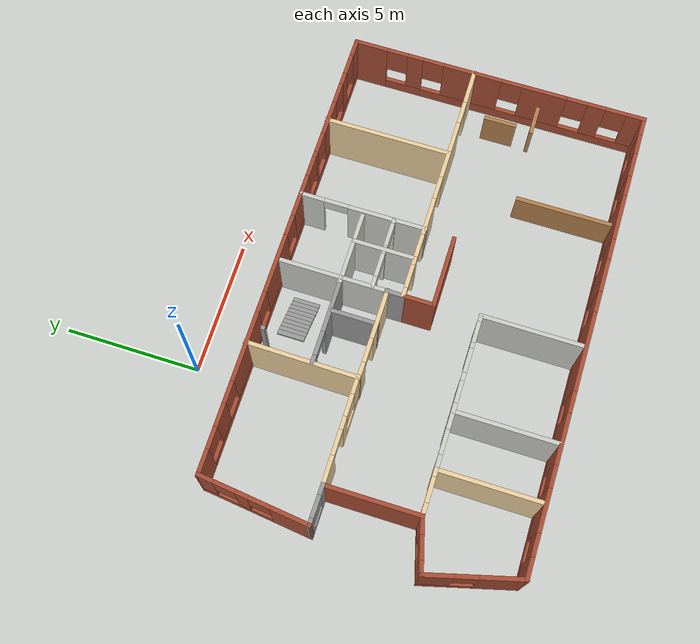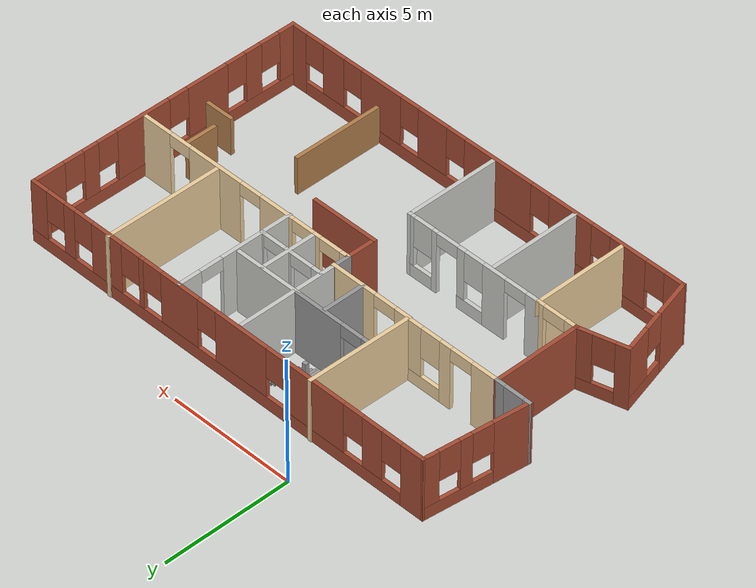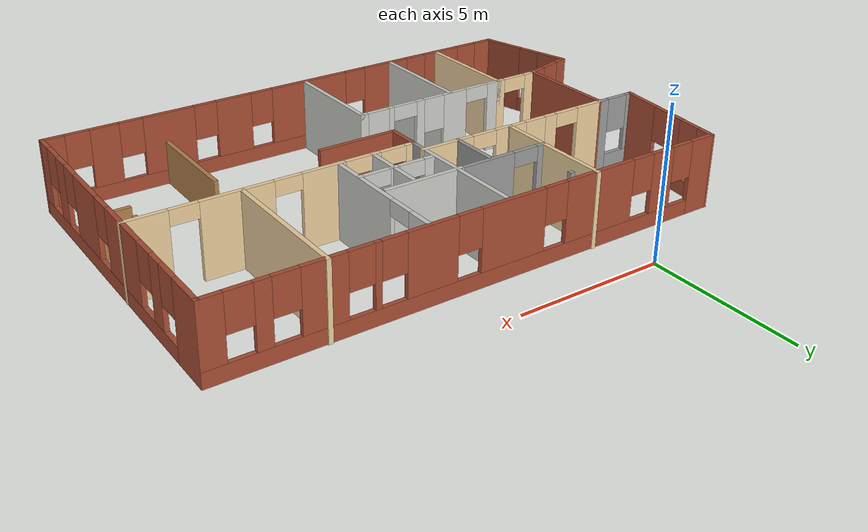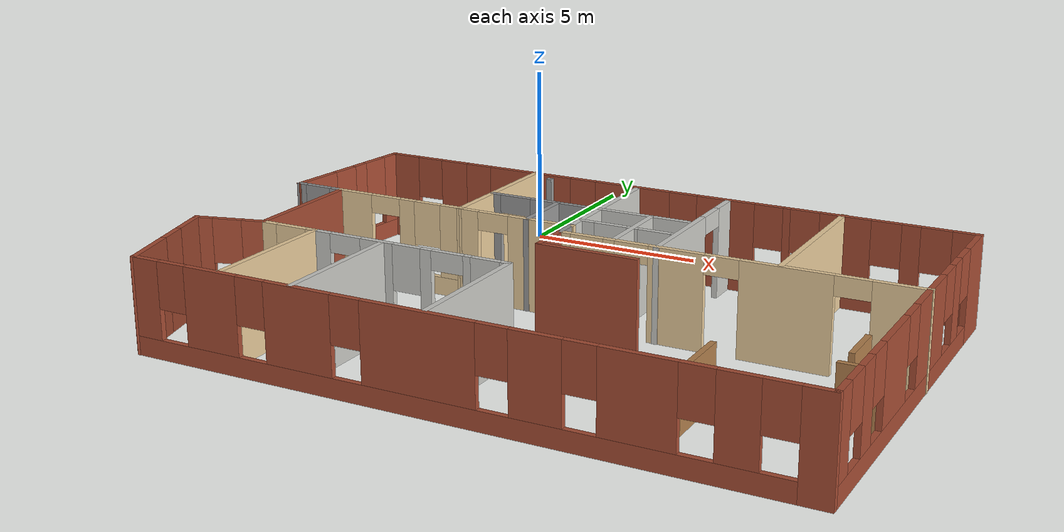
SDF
<?xml version='1.0'?>
<sdf version='1.6'>
  <model name='Building'>
    <pose frame=''>4.29574 -7.32604 0 0 -0 0</pose>
    <link name='Stairs_2'>
      <visual name='Stairs_2_Visual_0'>
        <pose frame=''>-0.680228 4.38796 0.05 0 0 -1.5708</pose>
        <geometry>
          <box>
            <size>1 0.18 0.1</size>
          </box>
        </geometry>
        <material>
          <script>
            <uri>file://media/materials/scripts/gazebo.material</uri>
            <name>Gazebo/Grey</name>
          </script>
          <ambient>1 1 1 1</ambient>
        </material>
        <meta>
          <layer>0</layer>
        </meta>
      </visual>
      <collision name='Stairs_2_Collision_0'>
        <geometry>
          <box>
            <size>1 0.18 0.1</size>
          </box>
        </geometry>
        <pose frame=''>-0.680228 4.38796 0.05 0 0 -1.5708</pose>
      </collision>
      <visual name='Stairs_2_Visual_1'>
        <pose frame=''>-0.860228 4.38796 0.15 0 0 -1.5708</pose>
        <geometry>
          <box>
            <size>1 0.18 0.1</size>
          </box>
        </geometry>
        <material>
          <script>
            <uri>file://media/materials/scripts/gazebo.material</uri>
            <name>Gazebo/Grey</name>
          </script>
          <ambient>1 1 1 1</ambient>
        </material>
        <meta>
          <layer>0</layer>
        </meta>
      </visual>
      <collision name='Stairs_2_Collision_1'>
        <geometry>
          <box>
            <size>1 0.18 0.1</size>
          </box>
        </geometry>
        <pose frame=''>-0.860228 4.38796 0.15 0 0 -1.5708</pose>
      </collision>
      <visual name='Stairs_2_Visual_2'>
        <pose frame=''>-1.04023 4.38796 0.25 0 0 -1.5708</pose>
        <geometry>
          <box>
            <size>1 0.18 0.1</size>
          </box>
        </geometry>
        <material>
          <script>
            <uri>file://media/materials/scripts/gazebo.material</uri>
            <name>Gazebo/Grey</name>
          </script>
          <ambient>1 1 1 1</ambient>
        </material>
        <meta>
          <layer>0</layer>
        </meta>
      </visual>
      <collision name='Stairs_2_Collision_2'>
        <geometry>
          <box>
            <size>1 0.18 0.1</size>
          </box>
        </geometry>
        <pose frame=''>-1.04023 4.38796 0.25 0 0 -1.5708</pose>
      </collision>
      <visual name='Stairs_2_Visual_3'>
        <pose frame=''>-1.22023 4.38796 0.35 0 0 -1.5708</pose>
        <geometry>
          <box>
            <size>1 0.18 0.1</size>
          </box>
        </geometry>
        <material>
          <script>
            <uri>file://media/materials/scripts/gazebo.material</uri>
            <name>Gazebo/Grey</name>
          </script>
          <ambient>1 1 1 1</ambient>
        </material>
        <meta>
          <layer>0</layer>
        </meta>
      </visual>
      <collision name='Stairs_2_Collision_3'>
        <geometry>
          <box>
            <size>1 0.18 0.1</size>
          </box>
        </geometry>
        <pose frame=''>-1.22023 4.38796 0.35 0 0 -1.5708</pose>
      </collision>
      <visual name='Stairs_2_Visual_4'>
        <pose frame=''>-1.40023 4.38796 0.45 0 0 -1.5708</pose>
        <geometry>
          <box>
            <size>1 0.18 0.1</size>
          </box>
        </geometry>
        <material>
          <script>
            <uri>file://media/materials/scripts/gazebo.material</uri>
            <name>Gazebo/Grey</name>
          </script>
          <ambient>1 1 1 1</ambient>
        </material>
        <meta>
          <layer>0</layer>
        </meta>
      </visual>
      <collision name='Stairs_2_Collision_4'>
        <geometry>
          <box>
            <size>1 0.18 0.1</size>
          </box>
        </geometry>
        <pose frame=''>-1.40023 4.38796 0.45 0 0 -1.5708</pose>
      </collision>
      <visual name='Stairs_2_Visual_5'>
        <pose frame=''>-1.58023 4.38796 0.55 0 0 -1.5708</pose>
        <geometry>
          <box>
            <size>1 0.18 0.1</size>
          </box>
        </geometry>
        <material>
          <script>
            <uri>file://media/materials/scripts/gazebo.material</uri>
            <name>Gazebo/Grey</name>
          </script>
          <ambient>1 1 1 1</ambient>
        </material>
        <meta>
          <layer>0</layer>
        </meta>
      </visual>
      <collision name='Stairs_2_Collision_5'>
        <geometry>
          <box>
            <size>1 0.18 0.1</size>
          </box>
        </geometry>
        <pose frame=''>-1.58023 4.38796 0.55 0 0 -1.5708</pose>
      </collision>
      <visual name='Stairs_2_Visual_6'>
        <pose frame=''>-1.76023 4.38796 0.65 0 0 -1.5708</pose>
        <geometry>
          <box>
            <size>1 0.18 0.1</size>
          </box>
        </geometry>
        <material>
          <script>
            <uri>file://media/materials/scripts/gazebo.material</uri>
            <name>Gazebo/Grey</name>
          </script>
          <ambient>1 1 1 1</ambient>
        </material>
        <meta>
          <layer>0</layer>
        </meta>
      </visual>
      <collision name='Stairs_2_Collision_6'>
        <geometry>
          <box>
            <size>1 0.18 0.1</size>
          </box>
        </geometry>
        <pose frame=''>-1.76023 4.38796 0.65 0 0 -1.5708</pose>
      </collision>
      <visual name='Stairs_2_Visual_7'>
        <pose frame=''>-1.94023 4.38796 0.75 0 0 -1.5708</pose>
        <geometry>
          <box>
            <size>1 0.18 0.1</size>
          </box>
        </geometry>
        <material>
          <script>
            <uri>file://media/materials/scripts/gazebo.material</uri>
            <name>Gazebo/Grey</name>
          </script>
          <ambient>1 1 1 1</ambient>
        </material>
        <meta>
          <layer>0</layer>
        </meta>
      </visual>
      <collision name='Stairs_2_Collision_7'>
        <geometry>
          <box>
            <size>1 0.18 0.1</size>
          </box>
        </geometry>
        <pose frame=''>-1.94023 4.38796 0.75 0 0 -1.5708</pose>
      </collision>
      <visual name='Stairs_2_Visual_8'>
        <pose frame=''>-2.12023 4.38796 0.85 0 0 -1.5708</pose>
        <geometry>
          <box>
            <size>1 0.18 0.1</size>
          </box>
        </geometry>
        <material>
          <script>
            <uri>file://media/materials/scripts/gazebo.material</uri>
            <name>Gazebo/Grey</name>
          </script>
          <ambient>1 1 1 1</ambient>
        </material>
        <meta>
          <layer>0</layer>
        </meta>
      </visual>
      <collision name='Stairs_2_Collision_8'>
        <geometry>
          <box>
            <size>1 0.18 0.1</size>
          </box>
        </geometry>
        <pose frame=''>-2.12023 4.38796 0.85 0 0 -1.5708</pose>
      </collision>
      <visual name='Stairs_2_Visual_9'>
        <pose frame=''>-2.30023 4.38796 0.95 0 0 -1.5708</pose>
        <geometry>
          <box>
            <size>1 0.18 0.1</size>
          </box>
        </geometry>
        <material>
          <script>
            <uri>file://media/materials/scripts/gazebo.material</uri>
            <name>Gazebo/Grey</name>
          </script>
          <ambient>1 1 1 1</ambient>
        </material>
        <meta>
          <layer>0</layer>
        </meta>
      </visual>
      <collision name='Stairs_2_Collision_9'>
        <geometry>
          <box>
            <size>1 0.18 0.1</size>
          </box>
        </geometry>
        <pose frame=''>-2.30023 4.38796 0.95 0 0 -1.5708</pose>
      </collision>
    </link>
    <link name='Wall_0'>
      <pose frame=''>0.434915 5.53865 0 0 -0 0</pose>
      <visual name='Wall_0_Visual_0'>
        <pose frame=''>-8.26944 0 1.25 0 -0 0</pose>
        <geometry>
          <box>
            <size>0.961111 0.15 2.5</size>
          </box>
        </geometry>
        <material>
          <script>
            <uri>file://media/materials/scripts/gazebo.material</uri>
            <name>Gazebo/Bricks</name>
          </script>
          <ambient>1 1 1 1</ambient>
        </material>
        <meta>
          <layer>0</layer>
        </meta>
      </visual>
      <collision name='Wall_0_Collision_0'>
        <geometry>
          <box>
            <size>0.961111 0.15 2.5</size>
          </box>
        </geometry>
        <pose frame=''>-8.26944 0 1.25 0 -0 0</pose>
      </collision>
      <visual name='Wall_0_Visual_1'>
        <pose frame=''>0.480555 0 0.25 0 -0 0</pose>
        <geometry>
          <box>
            <size>16.5389 0.15 0.5</size>
          </box>
        </geometry>
        <material>
          <script>
            <uri>file://media/materials/scripts/gazebo.material</uri>
            <name>Gazebo/Bricks</name>
          </script>
          <ambient>1 1 1 1</ambient>
        </material>
        <meta>
          <layer>0</layer>
        </meta>
      </visual>
      <collision name='Wall_0_Collision_1'>
        <geometry>
          <box>
            <size>16.5389 0.15 0.5</size>
          </box>
        </geometry>
        <pose frame=''>0.480555 0 0.25 0 -0 0</pose>
      </collision>
      <visual name='Wall_0_Visual_2'>
        <pose frame=''>-6.56423 0 1.5 0 -0 0</pose>
        <geometry>
          <box>
            <size>0.849313 0.15 2</size>
          </box>
        </geometry>
        <material>
          <script>
            <uri>file://media/materials/scripts/gazebo.material</uri>
            <name>Gazebo/Bricks</name>
          </script>
          <ambient>1 1 1 1</ambient>
        </material>
        <meta>
          <layer>0</layer>
        </meta>
      </visual>
      <collision name='Wall_0_Collision_2'>
        <geometry>
          <box>
            <size>0.849313 0.15 2</size>
          </box>
        </geometry>
        <pose frame=''>-6.56423 0 1.5 0 -0 0</pose>
      </collision>
      <visual name='Wall_0_Visual_3'>
        <pose frame=''>-4.04638 0 1.5 0 -0 0</pose>
        <geometry>
          <box>
            <size>2.5864 0.15 2</size>
          </box>
        </geometry>
        <material>
          <script>
            <uri>file://media/materials/scripts/gazebo.material</uri>
            <name>Gazebo/Bricks</name>
          </script>
          <ambient>1 1 1 1</ambient>
        </material>
        <meta>
          <layer>0</layer>
        </meta>
      </visual>
      <collision name='Wall_0_Collision_3'>
        <geometry>
          <box>
            <size>2.5864 0.15 2</size>
          </box>
        </geometry>
        <pose frame=''>-4.04638 0 1.5 0 -0 0</pose>
      </collision>
      <visual name='Wall_0_Visual_4'>
        <pose frame=''>-0.828204 0 1.5 0 -0 0</pose>
        <geometry>
          <box>
            <size>2.24994 0.15 2</size>
          </box>
        </geometry>
        <material>
          <script>
            <uri>file://media/materials/scripts/gazebo.material</uri>
            <name>Gazebo/Bricks</name>
          </script>
          <ambient>1 1 1 1</ambient>
        </material>
        <meta>
          <layer>0</layer>
        </meta>
      </visual>
      <collision name='Wall_0_Collision_4'>
        <geometry>
          <box>
            <size>2.24994 0.15 2</size>
          </box>
        </geometry>
        <pose frame=''>-0.828204 0 1.5 0 -0 0</pose>
      </collision>
      <visual name='Wall_0_Visual_5'>
        <pose frame=''>1.92369 0 1.5 0 -0 0</pose>
        <geometry>
          <box>
            <size>1.65386 0.15 2</size>
          </box>
        </geometry>
        <material>
          <script>
            <uri>file://media/materials/scripts/gazebo.material</uri>
            <name>Gazebo/Bricks</name>
          </script>
          <ambient>1 1 1 1</ambient>
        </material>
        <meta>
          <layer>0</layer>
        </meta>
      </visual>
      <collision name='Wall_0_Collision_5'>
        <geometry>
          <box>
            <size>1.65386 0.15 2</size>
          </box>
        </geometry>
        <pose frame=''>1.92369 0 1.5 0 -0 0</pose>
      </collision>
      <visual name='Wall_0_Visual_6'>
        <pose frame=''>3.65346 0 1.5 0 -0 0</pose>
        <geometry>
          <box>
            <size>0.205679 0.15 2</size>
          </box>
        </geometry>
        <material>
          <script>
            <uri>file://media/materials/scripts/gazebo.material</uri>
            <name>Gazebo/Bricks</name>
          </script>
          <ambient>1 1 1 1</ambient>
        </material>
        <meta>
          <layer>0</layer>
        </meta>
      </visual>
      <collision name='Wall_0_Collision_6'>
        <geometry>
          <box>
            <size>0.205679 0.15 2</size>
          </box>
        </geometry>
        <pose frame=''>3.65346 0 1.5 0 -0 0</pose>
      </collision>
      <visual name='Wall_0_Visual_7'>
        <pose frame=''>5.24243 0 1.5 0 -0 0</pose>
        <geometry>
          <box>
            <size>1.37227 0.15 2</size>
          </box>
        </geometry>
        <material>
          <script>
            <uri>file://media/materials/scripts/gazebo.material</uri>
            <name>Gazebo/Bricks</name>
          </script>
          <ambient>1 1 1 1</ambient>
        </material>
        <meta>
          <layer>0</layer>
        </meta>
      </visual>
      <collision name='Wall_0_Collision_7'>
        <geometry>
          <box>
            <size>1.37227 0.15 2</size>
          </box>
        </geometry>
        <pose frame=''>5.24243 0 1.5 0 -0 0</pose>
      </collision>
      <visual name='Wall_0_Visual_8'>
        <pose frame=''>6.9722 0 1.5 0 -0 0</pose>
        <geometry>
          <box>
            <size>0.487269 0.15 2</size>
          </box>
        </geometry>
        <material>
          <script>
            <uri>file://media/materials/scripts/gazebo.material</uri>
            <name>Gazebo/Bricks</name>
          </script>
          <ambient>1 1 1 1</ambient>
        </material>
        <meta>
          <layer>0</layer>
        </meta>
      </visual>
      <collision name='Wall_0_Collision_8'>
        <geometry>
          <box>
            <size>0.487269 0.15 2</size>
          </box>
        </geometry>
        <pose frame=''>6.9722 0 1.5 0 -0 0</pose>
      </collision>
      <visual name='Wall_0_Visual_9'>
        <pose frame=''>8.38292 0 1.5 0 -0 0</pose>
        <geometry>
          <box>
            <size>0.734164 0.15 2</size>
          </box>
        </geometry>
        <material>
          <script>
            <uri>file://media/materials/scripts/gazebo.material</uri>
            <name>Gazebo/Bricks</name>
          </script>
          <ambient>1 1 1 1</ambient>
        </material>
        <meta>
          <layer>0</layer>
        </meta>
      </visual>
      <collision name='Wall_0_Collision_9'>
        <geometry>
          <box>
            <size>0.734164 0.15 2</size>
          </box>
        </geometry>
        <pose frame=''>8.38292 0 1.5 0 -0 0</pose>
      </collision>
      <visual name='Wall_0_Visual_10'>
        <pose frame=''>-7.38889 0 1.9 0 -0 0</pose>
        <geometry>
          <box>
            <size>0.8 0.15 1.2</size>
          </box>
        </geometry>
        <material>
          <script>
            <uri>file://media/materials/scripts/gazebo.material</uri>
            <name>Gazebo/Bricks</name>
          </script>
          <ambient>1 1 1 1</ambient>
        </material>
        <meta>
          <layer>0</layer>
        </meta>
      </visual>
      <collision name='Wall_0_Collision_10'>
        <geometry>
          <box>
            <size>0.8 0.15 1.2</size>
          </box>
        </geometry>
        <pose frame=''>-7.38889 0 1.9 0 -0 0</pose>
      </collision>
      <visual name='Wall_0_Visual_11'>
        <pose frame=''>-5.73958 0 1.9 0 -0 0</pose>
        <geometry>
          <box>
            <size>0.8 0.15 1.2</size>
          </box>
        </geometry>
        <material>
          <script>
            <uri>file://media/materials/scripts/gazebo.material</uri>
            <name>Gazebo/Bricks</name>
          </script>
          <ambient>1 1 1 1</ambient>
        </material>
        <meta>
          <layer>0</layer>
        </meta>
      </visual>
      <collision name='Wall_0_Collision_11'>
        <geometry>
          <box>
            <size>0.8 0.15 1.2</size>
          </box>
        </geometry>
        <pose frame=''>-5.73958 0 1.9 0 -0 0</pose>
      </collision>
      <visual name='Wall_0_Visual_12'>
        <pose frame=''>-2.35317 0 1.9 0 -0 0</pose>
        <geometry>
          <box>
            <size>0.8 0.15 1.2</size>
          </box>
        </geometry>
        <material>
          <script>
            <uri>file://media/materials/scripts/gazebo.material</uri>
            <name>Gazebo/Bricks</name>
          </script>
          <ambient>1 1 1 1</ambient>
        </material>
        <meta>
          <layer>0</layer>
        </meta>
      </visual>
      <collision name='Wall_0_Collision_12'>
        <geometry>
          <box>
            <size>0.8 0.15 1.2</size>
          </box>
        </geometry>
        <pose frame=''>-2.35317 0 1.9 0 -0 0</pose>
      </collision>
      <visual name='Wall_0_Visual_13'>
        <pose frame=''>0.696767 0 1.9 0 -0 0</pose>
        <geometry>
          <box>
            <size>0.8 0.15 1.2</size>
          </box>
        </geometry>
        <material>
          <script>
            <uri>file://media/materials/scripts/gazebo.material</uri>
            <name>Gazebo/Bricks</name>
          </script>
          <ambient>1 1 1 1</ambient>
        </material>
        <meta>
          <layer>0</layer>
        </meta>
      </visual>
      <collision name='Wall_0_Collision_13'>
        <geometry>
          <box>
            <size>0.8 0.15 1.2</size>
          </box>
        </geometry>
        <pose frame=''>0.696767 0 1.9 0 -0 0</pose>
      </collision>
      <visual name='Wall_0_Visual_14'>
        <pose frame=''>3.15062 0 1.9 0 -0 0</pose>
        <geometry>
          <box>
            <size>0.8 0.15 1.2</size>
          </box>
        </geometry>
        <material>
          <script>
            <uri>file://media/materials/scripts/gazebo.material</uri>
            <name>Gazebo/Bricks</name>
          </script>
          <ambient>1 1 1 1</ambient>
        </material>
        <meta>
          <layer>0</layer>
        </meta>
      </visual>
      <collision name='Wall_0_Collision_14'>
        <geometry>
          <box>
            <size>0.8 0.15 1.2</size>
          </box>
        </geometry>
        <pose frame=''>3.15062 0 1.9 0 -0 0</pose>
      </collision>
      <visual name='Wall_0_Visual_15'>
        <pose frame=''>4.1563 0 1.9 0 -0 0</pose>
        <geometry>
          <box>
            <size>0.8 0.15 1.2</size>
          </box>
        </geometry>
        <material>
          <script>
            <uri>file://media/materials/scripts/gazebo.material</uri>
            <name>Gazebo/Bricks</name>
          </script>
          <ambient>1 1 1 1</ambient>
        </material>
        <meta>
          <layer>0</layer>
        </meta>
      </visual>
      <collision name='Wall_0_Collision_15'>
        <geometry>
          <box>
            <size>0.8 0.15 1.2</size>
          </box>
        </geometry>
        <pose frame=''>4.1563 0 1.9 0 -0 0</pose>
      </collision>
      <visual name='Wall_0_Visual_16'>
        <pose frame=''>6.32857 0 1.9 0 -0 0</pose>
        <geometry>
          <box>
            <size>0.8 0.15 1.2</size>
          </box>
        </geometry>
        <material>
          <script>
            <uri>file://media/materials/scripts/gazebo.material</uri>
            <name>Gazebo/Bricks</name>
          </script>
          <ambient>1 1 1 1</ambient>
        </material>
        <meta>
          <layer>0</layer>
        </meta>
      </visual>
      <collision name='Wall_0_Collision_16'>
        <geometry>
          <box>
            <size>0.8 0.15 1.2</size>
          </box>
        </geometry>
        <pose frame=''>6.32857 0 1.9 0 -0 0</pose>
      </collision>
      <visual name='Wall_0_Visual_17'>
        <pose frame=''>7.61584 0 1.9 0 -0 0</pose>
        <geometry>
          <box>
            <size>0.8 0.15 1.2</size>
          </box>
        </geometry>
        <material>
          <script>
            <uri>file://media/materials/scripts/gazebo.material</uri>
            <name>Gazebo/Bricks</name>
          </script>
          <ambient>1 1 1 1</ambient>
        </material>
        <meta>
          <layer>0</layer>
        </meta>
      </visual>
      <collision name='Wall_0_Collision_17'>
        <geometry>
          <box>
            <size>0.8 0.15 1.2</size>
          </box>
        </geometry>
        <pose frame=''>7.61584 0 1.9 0 -0 0</pose>
      </collision>
    </link>
    <link name='Wall_11'>
      <pose frame=''>-6.52017 -1.84669 0 0 -0 0</pose>
      <visual name='Wall_11_Visual_0'>
        <pose frame=''>-0.613993 0 1.25 0 -0 0</pose>
        <geometry>
          <box>
            <size>0.522013 0.15 2.5</size>
          </box>
        </geometry>
        <material>
          <script>
            <uri>file://media/materials/scripts/gazebo.material</uri>
            <name>Gazebo/Grey</name>
          </script>
          <ambient>0.921569 0.807843 0.615686 1</ambient>
        </material>
        <meta>
          <layer>0</layer>
        </meta>
      </visual>
      <collision name='Wall_11_Collision_0'>
        <geometry>
          <box>
            <size>0.522013 0.15 2.5</size>
          </box>
        </geometry>
        <pose frame=''>-0.613993 0 1.25 0 -0 0</pose>
      </collision>
      <visual name='Wall_11_Visual_1'>
        <pose frame=''>0.711007 0 1.25 0 -0 0</pose>
        <geometry>
          <box>
            <size>0.327987 0.15 2.5</size>
          </box>
        </geometry>
        <material>
          <script>
            <uri>file://media/materials/scripts/gazebo.material</uri>
            <name>Gazebo/Grey</name>
          </script>
          <ambient>0.921569 0.807843 0.615686 1</ambient>
        </material>
        <meta>
          <layer>0</layer>
        </meta>
      </visual>
      <collision name='Wall_11_Collision_1'>
        <geometry>
          <box>
            <size>0.327987 0.15 2.5</size>
          </box>
        </geometry>
        <pose frame=''>0.711007 0 1.25 0 -0 0</pose>
      </collision>
      <visual name='Wall_11_Visual_2'>
        <pose frame=''>0.097013 0 2.25 0 -0 0</pose>
        <geometry>
          <box>
            <size>0.9 0.15 0.5</size>
          </box>
        </geometry>
        <material>
          <script>
            <uri>file://media/materials/scripts/gazebo.material</uri>
            <name>Gazebo/Grey</name>
          </script>
          <ambient>0.921569 0.807843 0.615686 1</ambient>
        </material>
        <meta>
          <layer>0</layer>
        </meta>
      </visual>
      <collision name='Wall_11_Collision_2'>
        <geometry>
          <box>
            <size>0.9 0.15 0.5</size>
          </box>
        </geometry>
        <pose frame=''>0.097013 0 2.25 0 -0 0</pose>
      </collision>
    </link>
    <link name='Wall_12'>
      <collision name='Wall_12_Collision'>
        <geometry>
          <box>
            <size>3.75 0.15 2.5</size>
          </box>
        </geometry>
        <pose frame=''>0 0 1.25 0 -0 0</pose>
      </collision>
      <visual name='Wall_12_Visual'>
        <pose frame=''>0 0 1.25 0 -0 0</pose>
        <geometry>
          <box>
            <size>3.75 0.15 2.5</size>
          </box>
        </geometry>
        <material>
          <script>
            <uri>file://media/materials/scripts/gazebo.material</uri>
            <name>Gazebo/Grey</name>
          </script>
          <ambient>0.921569 0.807843 0.615686 1</ambient>
        </material>
        <meta>
          <layer>0</layer>
        </meta>
      </visual>
      <pose frame=''>-5.72017 -3.64669 0 0 0 -1.5708</pose>
    </link>
    <link name='Wall_14'>
      <pose frame=''>-2.92017 -1.84669 0 0 -0 0</pose>
      <visual name='Wall_14_Visual_0'>
        <pose frame=''>-2.58082 0 1.25 0 -0 0</pose>
        <geometry>
          <box>
            <size>0.588363 0.15 2.5</size>
          </box>
        </geometry>
        <material>
          <script>
            <uri>file://media/materials/scripts/gazebo.material</uri>
            <name>Gazebo/CeilingTiled</name>
          </script>
          <ambient>0.921569 0.807843 0.615686 1</ambient>
        </material>
        <meta>
          <layer>0</layer>
        </meta>
      </visual>
      <collision name='Wall_14_Collision_0'>
        <geometry>
          <box>
            <size>0.588363 0.15 2.5</size>
          </box>
        </geometry>
        <pose frame=''>-2.58082 0 1.25 0 -0 0</pose>
      </collision>
      <visual name='Wall_14_Visual_1'>
        <pose frame=''>-0.912337 0 1.25 0 -0 0</pose>
        <geometry>
          <box>
            <size>0.9486 0.15 2.5</size>
          </box>
        </geometry>
        <material>
          <script>
            <uri>file://media/materials/scripts/gazebo.material</uri>
            <name>Gazebo/CeilingTiled</name>
          </script>
          <ambient>0.921569 0.807843 0.615686 1</ambient>
        </material>
        <meta>
          <layer>0</layer>
        </meta>
      </visual>
      <collision name='Wall_14_Collision_1'>
        <geometry>
          <box>
            <size>0.9486 0.15 2.5</size>
          </box>
        </geometry>
        <pose frame=''>-0.912337 0 1.25 0 -0 0</pose>
      </collision>
      <visual name='Wall_14_Visual_2'>
        <pose frame=''>1.67976 0 1.25 0 -0 0</pose>
        <geometry>
          <box>
            <size>0.208 0.15 2.5</size>
          </box>
        </geometry>
        <material>
          <script>
            <uri>file://media/materials/scripts/gazebo.material</uri>
            <name>Gazebo/CeilingTiled</name>
          </script>
          <ambient>0.921569 0.807843 0.615686 1</ambient>
        </material>
        <meta>
          <layer>0</layer>
        </meta>
      </visual>
      <collision name='Wall_14_Collision_2'>
        <geometry>
          <box>
            <size>0.208 0.15 2.5</size>
          </box>
        </geometry>
        <pose frame=''>1.67976 0 1.25 0 -0 0</pose>
      </collision>
      <visual name='Wall_14_Visual_3'>
        <pose frame=''>0.118863 0 0.25 0 -0 0</pose>
        <geometry>
          <box>
            <size>1.1138 0.15 0.5</size>
          </box>
        </geometry>
        <material>
          <script>
            <uri>file://media/materials/scripts/gazebo.material</uri>
            <name>Gazebo/CeilingTiled</name>
          </script>
          <ambient>0.921569 0.807843 0.615686 1</ambient>
        </material>
        <meta>
          <layer>0</layer>
        </meta>
      </visual>
      <collision name='Wall_14_Collision_3'>
        <geometry>
          <box>
            <size>1.1138 0.15 0.5</size>
          </box>
        </geometry>
        <pose frame=''>0.118863 0 0.25 0 -0 0</pose>
      </collision>
      <visual name='Wall_14_Visual_4'>
        <pose frame=''>2.32938 0 0.25 0 -0 0</pose>
        <geometry>
          <box>
            <size>1.09124 0.15 0.5</size>
          </box>
        </geometry>
        <material>
          <script>
            <uri>file://media/materials/scripts/gazebo.material</uri>
            <name>Gazebo/CeilingTiled</name>
          </script>
          <ambient>0.921569 0.807843 0.615686 1</ambient>
        </material>
        <meta>
          <layer>0</layer>
        </meta>
      </visual>
      <collision name='Wall_14_Collision_4'>
        <geometry>
          <box>
            <size>1.09124 0.15 0.5</size>
          </box>
        </geometry>
        <pose frame=''>2.32938 0 0.25 0 -0 0</pose>
      </collision>
      <visual name='Wall_14_Visual_5'>
        <pose frame=''>0.518863 0 1.5 0 -0 0</pose>
        <geometry>
          <box>
            <size>0.3138 0.15 2</size>
          </box>
        </geometry>
        <material>
          <script>
            <uri>file://media/materials/scripts/gazebo.material</uri>
            <name>Gazebo/CeilingTiled</name>
          </script>
          <ambient>0.921569 0.807843 0.615686 1</ambient>
        </material>
        <meta>
          <layer>0</layer>
        </meta>
      </visual>
      <collision name='Wall_14_Collision_5'>
        <geometry>
          <box>
            <size>0.3138 0.15 2</size>
          </box>
        </geometry>
        <pose frame=''>0.518863 0 1.5 0 -0 0</pose>
      </collision>
      <visual name='Wall_14_Visual_6'>
        <pose frame=''>0.518863 0 1.5 0 -0 0</pose>
        <geometry>
          <box>
            <size>0.3138 0.15 2</size>
          </box>
        </geometry>
        <material>
          <script>
            <uri>file://media/materials/scripts/gazebo.material</uri>
            <name>Gazebo/CeilingTiled</name>
          </script>
          <ambient>0.921569 0.807843 0.615686 1</ambient>
        </material>
        <meta>
          <layer>0</layer>
        </meta>
      </visual>
      <collision name='Wall_14_Collision_6'>
        <geometry>
          <box>
            <size>0.3138 0.15 2</size>
          </box>
        </geometry>
        <pose frame=''>0.518863 0 1.5 0 -0 0</pose>
      </collision>
      <visual name='Wall_14_Visual_7'>
        <pose frame=''>2.72938 0 1.5 0 -0 0</pose>
        <geometry>
          <box>
            <size>0.291237 0.15 2</size>
          </box>
        </geometry>
        <material>
          <script>
            <uri>file://media/materials/scripts/gazebo.material</uri>
            <name>Gazebo/CeilingTiled</name>
          </script>
          <ambient>0.921569 0.807843 0.615686 1</ambient>
        </material>
        <meta>
          <layer>0</layer>
        </meta>
      </visual>
      <collision name='Wall_14_Collision_7'>
        <geometry>
          <box>
            <size>0.291237 0.15 2</size>
          </box>
        </geometry>
        <pose frame=''>2.72938 0 1.5 0 -0 0</pose>
      </collision>
      <visual name='Wall_14_Visual_8'>
        <pose frame=''>-0.038037 0 1.9 0 -0 0</pose>
        <geometry>
          <box>
            <size>0.8 0.15 1.2</size>
          </box>
        </geometry>
        <material>
          <script>
            <uri>file://media/materials/scripts/gazebo.material</uri>
            <name>Gazebo/CeilingTiled</name>
          </script>
          <ambient>0.921569 0.807843 0.615686 1</ambient>
        </material>
        <meta>
          <layer>0</layer>
        </meta>
      </visual>
      <collision name='Wall_14_Collision_8'>
        <geometry>
          <box>
            <size>0.8 0.15 1.2</size>
          </box>
        </geometry>
        <pose frame=''>-0.038037 0 1.9 0 -0 0</pose>
      </collision>
      <visual name='Wall_14_Visual_9'>
        <pose frame=''>2.18376 0 1.9 0 -0 0</pose>
        <geometry>
          <box>
            <size>0.8 0.15 1.2</size>
          </box>
        </geometry>
        <material>
          <script>
            <uri>file://media/materials/scripts/gazebo.material</uri>
            <name>Gazebo/CeilingTiled</name>
          </script>
          <ambient>0.921569 0.807843 0.615686 1</ambient>
        </material>
        <meta>
          <layer>0</layer>
        </meta>
      </visual>
      <collision name='Wall_14_Collision_9'>
        <geometry>
          <box>
            <size>0.8 0.15 1.2</size>
          </box>
        </geometry>
        <pose frame=''>2.18376 0 1.9 0 -0 0</pose>
      </collision>
      <visual name='Wall_14_Visual_10'>
        <pose frame=''>-1.83664 0 2.25 0 -0 0</pose>
        <geometry>
          <box>
            <size>0.9 0.15 0.5</size>
          </box>
        </geometry>
        <material>
          <script>
            <uri>file://media/materials/scripts/gazebo.material</uri>
            <name>Gazebo/CeilingTiled</name>
          </script>
          <ambient>0.921569 0.807843 0.615686 1</ambient>
        </material>
        <meta>
          <layer>0</layer>
        </meta>
      </visual>
      <collision name='Wall_14_Collision_10'>
        <geometry>
          <box>
            <size>0.9 0.15 0.5</size>
          </box>
        </geometry>
        <pose frame=''>-1.83664 0 2.25 0 -0 0</pose>
      </collision>
      <visual name='Wall_14_Visual_11'>
        <pose frame=''>1.12576 0 2.25 0 -0 0</pose>
        <geometry>
          <box>
            <size>0.9 0.15 0.5</size>
          </box>
        </geometry>
        <material>
          <script>
            <uri>file://media/materials/scripts/gazebo.material</uri>
            <name>Gazebo/CeilingTiled</name>
          </script>
          <ambient>0.921569 0.807843 0.615686 1</ambient>
        </material>
        <meta>
          <layer>0</layer>
        </meta>
      </visual>
      <collision name='Wall_14_Collision_11'>
        <geometry>
          <box>
            <size>0.9 0.15 0.5</size>
          </box>
        </geometry>
        <pose frame=''>1.12576 0 2.25 0 -0 0</pose>
      </collision>
      <visual name='Wall_14_Visual_12'>
        <pose frame=''>1.12576 0 2.25 0 -0 0</pose>
        <geometry>
          <box>
            <size>0.9 0.15 0.5</size>
          </box>
        </geometry>
        <material>
          <script>
            <uri>file://media/materials/scripts/gazebo.material</uri>
            <name>Gazebo/CeilingTiled</name>
          </script>
          <ambient>0.921569 0.807843 0.615686 1</ambient>
        </material>
        <meta>
          <layer>0</layer>
        </meta>
      </visual>
      <collision name='Wall_14_Collision_12'>
        <geometry>
          <box>
            <size>0.9 0.15 0.5</size>
          </box>
        </geometry>
        <pose frame=''>1.12576 0 2.25 0 -0 0</pose>
      </collision>
    </link>
    <link name='Wall_15'>
      <collision name='Wall_15_Collision'>
        <geometry>
          <box>
            <size>3.75 0.15 2.5</size>
          </box>
        </geometry>
        <pose frame=''>0 0 1.25 0 -0 0</pose>
      </collision>
      <visual name='Wall_15_Visual'>
        <pose frame=''>0 0 1.25 0 -0 0</pose>
        <geometry>
          <box>
            <size>3.75 0.15 2.5</size>
          </box>
        </geometry>
        <material>
          <script>
            <uri>file://media/materials/scripts/gazebo.material</uri>
            <name>Gazebo/CeilingTiled</name>
          </script>
          <ambient>0.921569 0.807843 0.615686 1</ambient>
        </material>
        <meta>
          <layer>0</layer>
        </meta>
      </visual>
      <pose frame=''>-0.120167 -3.64669 0 0 0 -1.5708</pose>
    </link>
    <link name='Wall_19'>
      <collision name='Wall_19_Collision'>
        <geometry>
          <box>
            <size>3.75 0.15 2.5</size>
          </box>
        </geometry>
        <pose frame=''>0 0 1.25 0 -0 0</pose>
      </collision>
      <visual name='Wall_19_Visual'>
        <pose frame=''>0 0 1.25 0 -0 0</pose>
        <geometry>
          <box>
            <size>3.75 0.15 2.5</size>
          </box>
        </geometry>
        <material>
          <script>
            <uri>file://media/materials/scripts/gazebo.material</uri>
            <name>Gazebo/CeilingTiled</name>
          </script>
          <ambient>0.921569 0.807843 0.615686 1</ambient>
        </material>
        <meta>
          <layer>0</layer>
        </meta>
      </visual>
      <pose frame=''>-3.66538 -3.70743 0 0 0 -1.5708</pose>
    </link>
    <link name='Wall_2'>
      <pose frame=''>9.10991 -0.011353 0 0 0 -1.5708</pose>
      <visual name='Wall_2_Visual_0'>
        <pose frame=''>-4.96991 0 1.25 0 -0 0</pose>
        <geometry>
          <box>
            <size>1.31017 0.15 2.5</size>
          </box>
        </geometry>
        <material>
          <script>
            <uri>file://media/materials/scripts/gazebo.material</uri>
            <name>Gazebo/Bricks</name>
          </script>
          <ambient>0 0.666667 0.498039 1</ambient>
        </material>
        <meta>
          <layer>0</layer>
        </meta>
      </visual>
      <collision name='Wall_2_Collision_0'>
        <geometry>
          <box>
            <size>1.31017 0.15 2.5</size>
          </box>
        </geometry>
        <pose frame=''>-4.96991 0 1.25 0 -0 0</pose>
      </collision>
      <visual name='Wall_2_Visual_1'>
        <pose frame=''>0.655087 0 0.25 0 -0 0</pose>
        <geometry>
          <box>
            <size>9.93983 0.15 0.5</size>
          </box>
        </geometry>
        <material>
          <script>
            <uri>file://media/materials/scripts/gazebo.material</uri>
            <name>Gazebo/Bricks</name>
          </script>
          <ambient>0 0.666667 0.498039 1</ambient>
        </material>
        <meta>
          <layer>0</layer>
        </meta>
      </visual>
      <collision name='Wall_2_Collision_1'>
        <geometry>
          <box>
            <size>9.93983 0.15 0.5</size>
          </box>
        </geometry>
        <pose frame=''>0.655087 0 0.25 0 -0 0</pose>
      </collision>
      <visual name='Wall_2_Visual_2'>
        <pose frame=''>-3.21085 0 1.5 0 -0 0</pose>
        <geometry>
          <box>
            <size>0.60795 0.15 2</size>
          </box>
        </geometry>
        <material>
          <script>
            <uri>file://media/materials/scripts/gazebo.material</uri>
            <name>Gazebo/Bricks</name>
          </script>
          <ambient>0 0.666667 0.498039 1</ambient>
        </material>
        <meta>
          <layer>0</layer>
        </meta>
      </visual>
      <collision name='Wall_2_Collision_2'>
        <geometry>
          <box>
            <size>0.60795 0.15 2</size>
          </box>
        </geometry>
        <pose frame=''>-3.21085 0 1.5 0 -0 0</pose>
      </collision>
      <visual name='Wall_2_Visual_3'>
        <pose frame=''>-0.992199 0 1.5 0 -0 0</pose>
        <geometry>
          <box>
            <size>2.22935 0.15 2</size>
          </box>
        </geometry>
        <material>
          <script>
            <uri>file://media/materials/scripts/gazebo.material</uri>
            <name>Gazebo/Bricks</name>
          </script>
          <ambient>0 0.666667 0.498039 1</ambient>
        </material>
        <meta>
          <layer>0</layer>
        </meta>
      </visual>
      <collision name='Wall_2_Collision_3'>
        <geometry>
          <box>
            <size>2.22935 0.15 2</size>
          </box>
        </geometry>
        <pose frame=''>-0.992199 0 1.5 0 -0 0</pose>
      </collision>
      <visual name='Wall_2_Visual_4'>
        <pose frame=''>1.77153 0 1.5 0 -0 0</pose>
        <geometry>
          <box>
            <size>1.69811 0.15 2</size>
          </box>
        </geometry>
        <material>
          <script>
            <uri>file://media/materials/scripts/gazebo.material</uri>
            <name>Gazebo/Bricks</name>
          </script>
          <ambient>0 0.666667 0.498039 1</ambient>
        </material>
        <meta>
          <layer>0</layer>
        </meta>
      </visual>
      <collision name='Wall_2_Collision_4'>
        <geometry>
          <box>
            <size>1.69811 0.15 2</size>
          </box>
        </geometry>
        <pose frame=''>1.77153 0 1.5 0 -0 0</pose>
      </collision>
      <visual name='Wall_2_Visual_5'>
        <pose frame=''>3.76076 0 1.5 0 -0 0</pose>
        <geometry>
          <box>
            <size>0.680358 0.15 2</size>
          </box>
        </geometry>
        <material>
          <script>
            <uri>file://media/materials/scripts/gazebo.material</uri>
            <name>Gazebo/Bricks</name>
          </script>
          <ambient>0 0.666667 0.498039 1</ambient>
        </material>
        <meta>
          <layer>0</layer>
        </meta>
      </visual>
      <collision name='Wall_2_Collision_5'>
        <geometry>
          <box>
            <size>0.680358 0.15 2</size>
          </box>
        </geometry>
        <pose frame=''>3.76076 0 1.5 0 -0 0</pose>
      </collision>
      <visual name='Wall_2_Visual_6'>
        <pose frame=''>5.26297 0 1.5 0 -0 0</pose>
        <geometry>
          <box>
            <size>0.724057 0.15 2</size>
          </box>
        </geometry>
        <material>
          <script>
            <uri>file://media/materials/scripts/gazebo.material</uri>
            <name>Gazebo/Bricks</name>
          </script>
          <ambient>0 0.666667 0.498039 1</ambient>
        </material>
        <meta>
          <layer>0</layer>
        </meta>
      </visual>
      <collision name='Wall_2_Collision_6'>
        <geometry>
          <box>
            <size>0.724057 0.15 2</size>
          </box>
        </geometry>
        <pose frame=''>5.26297 0 1.5 0 -0 0</pose>
      </collision>
      <visual name='Wall_2_Visual_7'>
        <pose frame=''>-3.91483 0 1.9 0 -0 0</pose>
        <geometry>
          <box>
            <size>0.8 0.15 1.2</size>
          </box>
        </geometry>
        <material>
          <script>
            <uri>file://media/materials/scripts/gazebo.material</uri>
            <name>Gazebo/Bricks</name>
          </script>
          <ambient>0 0.666667 0.498039 1</ambient>
        </material>
        <meta>
          <layer>0</layer>
        </meta>
      </visual>
      <collision name='Wall_2_Collision_7'>
        <geometry>
          <box>
            <size>0.8 0.15 1.2</size>
          </box>
        </geometry>
        <pose frame=''>-3.91483 0 1.9 0 -0 0</pose>
      </collision>
      <visual name='Wall_2_Visual_8'>
        <pose frame=''>-2.50688 0 1.9 0 -0 0</pose>
        <geometry>
          <box>
            <size>0.8 0.15 1.2</size>
          </box>
        </geometry>
        <material>
          <script>
            <uri>file://media/materials/scripts/gazebo.material</uri>
            <name>Gazebo/Bricks</name>
          </script>
          <ambient>0 0.666667 0.498039 1</ambient>
        </material>
        <meta>
          <layer>0</layer>
        </meta>
      </visual>
      <collision name='Wall_2_Collision_8'>
        <geometry>
          <box>
            <size>0.8 0.15 1.2</size>
          </box>
        </geometry>
        <pose frame=''>-2.50688 0 1.9 0 -0 0</pose>
      </collision>
      <visual name='Wall_2_Visual_9'>
        <pose frame=''>0.522479 0 1.9 0 -0 0</pose>
        <geometry>
          <box>
            <size>0.8 0.15 1.2</size>
          </box>
        </geometry>
        <material>
          <script>
            <uri>file://media/materials/scripts/gazebo.material</uri>
            <name>Gazebo/Bricks</name>
          </script>
          <ambient>0 0.666667 0.498039 1</ambient>
        </material>
        <meta>
          <layer>0</layer>
        </meta>
      </visual>
      <collision name='Wall_2_Collision_9'>
        <geometry>
          <box>
            <size>0.8 0.15 1.2</size>
          </box>
        </geometry>
        <pose frame=''>0.522479 0 1.9 0 -0 0</pose>
      </collision>
      <visual name='Wall_2_Visual_10'>
        <pose frame=''>3.02059 0 1.9 0 -0 0</pose>
        <geometry>
          <box>
            <size>0.8 0.15 1.2</size>
          </box>
        </geometry>
        <material>
          <script>
            <uri>file://media/materials/scripts/gazebo.material</uri>
            <name>Gazebo/Bricks</name>
          </script>
          <ambient>0 0.666667 0.498039 1</ambient>
        </material>
        <meta>
          <layer>0</layer>
        </meta>
      </visual>
      <collision name='Wall_2_Collision_10'>
        <geometry>
          <box>
            <size>0.8 0.15 1.2</size>
          </box>
        </geometry>
        <pose frame=''>3.02059 0 1.9 0 -0 0</pose>
      </collision>
      <visual name='Wall_2_Visual_11'>
        <pose frame=''>4.50094 0 1.9 0 -0 0</pose>
        <geometry>
          <box>
            <size>0.8 0.15 1.2</size>
          </box>
        </geometry>
        <material>
          <script>
            <uri>file://media/materials/scripts/gazebo.material</uri>
            <name>Gazebo/Bricks</name>
          </script>
          <ambient>0 0.666667 0.498039 1</ambient>
        </material>
        <meta>
          <layer>0</layer>
        </meta>
      </visual>
      <collision name='Wall_2_Collision_11'>
        <geometry>
          <box>
            <size>0.8 0.15 1.2</size>
          </box>
        </geometry>
        <pose frame=''>4.50094 0 1.9 0 -0 0</pose>
      </collision>
    </link>
    <link name='Wall_21'>
      <collision name='Wall_21_Collision'>
        <geometry>
          <box>
            <size>3.75 0.15 1.5</size>
          </box>
        </geometry>
        <pose frame=''>0 0 0.75 0 -0 0</pose>
      </collision>
      <visual name='Wall_21_Visual'>
        <pose frame=''>0 0 0.75 0 -0 0</pose>
        <geometry>
          <box>
            <size>3.75 0.15 1.5</size>
          </box>
        </geometry>
        <material>
          <script>
            <uri>file://media/materials/scripts/gazebo.material</uri>
            <name>Gazebo/Wood</name>
          </script>
          <ambient>1 1 1 1</ambient>
        </material>
        <meta>
          <layer>0</layer>
        </meta>
      </visual>
      <pose frame=''>5.09526 -3.75796 0 0 -0 1.5708</pose>
    </link>
    <link name='Wall_23'>
      <pose frame=''>-5.40433 1.5402 0 0 -0 0</pose>
      <visual name='Wall_23_Visual_0'>
        <pose frame=''>-1.44346 0 1.25 0 -0 0</pose>
        <geometry>
          <box>
            <size>1.11308 0.15 2.5</size>
          </box>
        </geometry>
        <material>
          <script>
            <uri>file://media/materials/scripts/gazebo.material</uri>
            <name>Gazebo/Grey</name>
          </script>
          <ambient>0.921569 0.807843 0.615686 1</ambient>
        </material>
        <meta>
          <layer>0</layer>
        </meta>
      </visual>
      <collision name='Wall_23_Collision_0'>
        <geometry>
          <box>
            <size>1.11308 0.15 2.5</size>
          </box>
        </geometry>
        <pose frame=''>-1.44346 0 1.25 0 -0 0</pose>
      </collision>
      <visual name='Wall_23_Visual_1'>
        <pose frame=''>0.249326 0 1.25 0 -0 0</pose>
        <geometry>
          <box>
            <size>0.4725 0.15 2.5</size>
          </box>
        </geometry>
        <material>
          <script>
            <uri>file://media/materials/scripts/gazebo.material</uri>
            <name>Gazebo/Grey</name>
          </script>
          <ambient>0.921569 0.807843 0.615686 1</ambient>
        </material>
        <meta>
          <layer>0</layer>
        </meta>
      </visual>
      <collision name='Wall_23_Collision_1'>
        <geometry>
          <box>
            <size>0.4725 0.15 2.5</size>
          </box>
        </geometry>
        <pose frame=''>0.249326 0 1.25 0 -0 0</pose>
      </collision>
      <visual name='Wall_23_Visual_2'>
        <pose frame=''>1.24279 0 0.25 0 -0 0</pose>
        <geometry>
          <box>
            <size>1.51442 0.15 0.5</size>
          </box>
        </geometry>
        <material>
          <script>
            <uri>file://media/materials/scripts/gazebo.material</uri>
            <name>Gazebo/Grey</name>
          </script>
          <ambient>0.921569 0.807843 0.615686 1</ambient>
        </material>
        <meta>
          <layer>0</layer>
        </meta>
      </visual>
      <collision name='Wall_23_Collision_2'>
        <geometry>
          <box>
            <size>1.51442 0.15 0.5</size>
          </box>
        </geometry>
        <pose frame=''>1.24279 0 0.25 0 -0 0</pose>
      </collision>
      <visual name='Wall_23_Visual_3'>
        <pose frame=''>1.64279 0 1.5 0 -0 0</pose>
        <geometry>
          <box>
            <size>0.714424 0.15 2</size>
          </box>
        </geometry>
        <material>
          <script>
            <uri>file://media/materials/scripts/gazebo.material</uri>
            <name>Gazebo/Grey</name>
          </script>
          <ambient>0.921569 0.807843 0.615686 1</ambient>
        </material>
        <meta>
          <layer>0</layer>
        </meta>
      </visual>
      <collision name='Wall_23_Collision_3'>
        <geometry>
          <box>
            <size>0.714424 0.15 2</size>
          </box>
        </geometry>
        <pose frame=''>1.64279 0 1.5 0 -0 0</pose>
      </collision>
      <visual name='Wall_23_Visual_4'>
        <pose frame=''>0.885576 0 1.9 0 -0 0</pose>
        <geometry>
          <box>
            <size>0.8 0.15 1.2</size>
          </box>
        </geometry>
        <material>
          <script>
            <uri>file://media/materials/scripts/gazebo.material</uri>
            <name>Gazebo/Grey</name>
          </script>
          <ambient>0.921569 0.807843 0.615686 1</ambient>
        </material>
        <meta>
          <layer>0</layer>
        </meta>
      </visual>
      <collision name='Wall_23_Collision_4'>
        <geometry>
          <box>
            <size>0.8 0.15 1.2</size>
          </box>
        </geometry>
        <pose frame=''>0.885576 0 1.9 0 -0 0</pose>
      </collision>
      <visual name='Wall_23_Visual_5'>
        <pose frame=''>-0.436924 0 2.25 0 -0 0</pose>
        <geometry>
          <box>
            <size>0.9 0.15 0.5</size>
          </box>
        </geometry>
        <material>
          <script>
            <uri>file://media/materials/scripts/gazebo.material</uri>
            <name>Gazebo/Grey</name>
          </script>
          <ambient>0.921569 0.807843 0.615686 1</ambient>
        </material>
        <meta>
          <layer>0</layer>
        </meta>
      </visual>
      <collision name='Wall_23_Collision_5'>
        <geometry>
          <box>
            <size>0.9 0.15 0.5</size>
          </box>
        </geometry>
        <pose frame=''>-0.436924 0 2.25 0 -0 0</pose>
      </collision>
    </link>
    <link name='Wall_27'>
      <collision name='Wall_27_Collision'>
        <geometry>
          <box>
            <size>0.15 0.15 2.5</size>
          </box>
        </geometry>
        <pose frame=''>0 0 1.25 0 -0 0</pose>
      </collision>
      <visual name='Wall_27_Visual'>
        <pose frame=''>0 0 1.25 0 -0 0</pose>
        <geometry>
          <box>
            <size>0.15 0.15 2.5</size>
          </box>
        </geometry>
        <material>
          <script>
            <uri>file://media/materials/scripts/gazebo.material</uri>
            <name>Gazebo/Grey</name>
          </script>
          <ambient>1 1 1 1</ambient>
        </material>
        <meta>
          <layer>0</layer>
        </meta>
      </visual>
      <pose frame=''>-2.80058 5.17081 0 0 -0 0</pose>
    </link>
    <link name='Wall_3'>
      <pose frame=''>0.434915 -5.56135 0 0 -0 3.14159</pose>
      <visual name='Wall_3_Visual_0'>
        <pose frame=''>-8.37149 0 1.25 0 -0 0</pose>
        <geometry>
          <box>
            <size>0.757013 0.15 2.5</size>
          </box>
        </geometry>
        <material>
          <script>
            <uri>file://media/materials/scripts/gazebo.material</uri>
            <name>Gazebo/Bricks</name>
          </script>
          <ambient>1 1 1 1</ambient>
        </material>
        <meta>
          <layer>0</layer>
        </meta>
      </visual>
      <collision name='Wall_3_Collision_0'>
        <geometry>
          <box>
            <size>0.757013 0.15 2.5</size>
          </box>
        </geometry>
        <pose frame=''>-8.37149 0 1.25 0 -0 0</pose>
      </collision>
      <visual name='Wall_3_Visual_1'>
        <pose frame=''>0.378507 0 0.25 0 -0 0</pose>
        <geometry>
          <box>
            <size>16.743 0.15 0.5</size>
          </box>
        </geometry>
        <material>
          <script>
            <uri>file://media/materials/scripts/gazebo.material</uri>
            <name>Gazebo/Bricks</name>
          </script>
          <ambient>1 1 1 1</ambient>
        </material>
        <meta>
          <layer>0</layer>
        </meta>
      </visual>
      <collision name='Wall_3_Collision_1'>
        <geometry>
          <box>
            <size>16.743 0.15 0.5</size>
          </box>
        </geometry>
        <pose frame=''>0.378507 0 0.25 0 -0 0</pose>
      </collision>
      <visual name='Wall_3_Visual_2'>
        <pose frame=''>-6.71402 0 1.5 0 -0 0</pose>
        <geometry>
          <box>
            <size>0.957926 0.15 2</size>
          </box>
        </geometry>
        <material>
          <script>
            <uri>file://media/materials/scripts/gazebo.material</uri>
            <name>Gazebo/Bricks</name>
          </script>
          <ambient>1 1 1 1</ambient>
        </material>
        <meta>
          <layer>0</layer>
        </meta>
      </visual>
      <collision name='Wall_3_Collision_2'>
        <geometry>
          <box>
            <size>0.957926 0.15 2</size>
          </box>
        </geometry>
        <pose frame=''>-6.71402 0 1.5 0 -0 0</pose>
      </collision>
      <visual name='Wall_3_Visual_3'>
        <pose frame=''>-4.53975 0 1.5 0 -0 0</pose>
        <geometry>
          <box>
            <size>1.79063 0.15 2</size>
          </box>
        </geometry>
        <material>
          <script>
            <uri>file://media/materials/scripts/gazebo.material</uri>
            <name>Gazebo/Bricks</name>
          </script>
          <ambient>1 1 1 1</ambient>
        </material>
        <meta>
          <layer>0</layer>
        </meta>
      </visual>
      <collision name='Wall_3_Collision_3'>
        <geometry>
          <box>
            <size>1.79063 0.15 2</size>
          </box>
        </geometry>
        <pose frame=''>-4.53975 0 1.5 0 -0 0</pose>
      </collision>
      <visual name='Wall_3_Visual_4'>
        <pose frame=''>-2.20356 0 1.5 0 -0 0</pose>
        <geometry>
          <box>
            <size>1.28175 0.15 2</size>
          </box>
        </geometry>
        <material>
          <script>
            <uri>file://media/materials/scripts/gazebo.material</uri>
            <name>Gazebo/Bricks</name>
          </script>
          <ambient>1 1 1 1</ambient>
        </material>
        <meta>
          <layer>0</layer>
        </meta>
      </visual>
      <collision name='Wall_3_Collision_4'>
        <geometry>
          <box>
            <size>1.28175 0.15 2</size>
          </box>
        </geometry>
        <pose frame=''>-2.20356 0 1.5 0 -0 0</pose>
      </collision>
      <visual name='Wall_3_Visual_5'>
        <pose frame=''>0.710901 0 1.5 0 -0 0</pose>
        <geometry>
          <box>
            <size>2.94716 0.15 2</size>
          </box>
        </geometry>
        <material>
          <script>
            <uri>file://media/materials/scripts/gazebo.material</uri>
            <name>Gazebo/Bricks</name>
          </script>
          <ambient>1 1 1 1</ambient>
        </material>
        <meta>
          <layer>0</layer>
        </meta>
      </visual>
      <collision name='Wall_3_Collision_5'>
        <geometry>
          <box>
            <size>2.94716 0.15 2</size>
          </box>
        </geometry>
        <pose frame=''>0.710901 0 1.5 0 -0 0</pose>
      </collision>
      <visual name='Wall_3_Visual_6'>
        <pose frame=''>3.90293 0 1.5 0 -0 0</pose>
        <geometry>
          <box>
            <size>1.83689 0.15 2</size>
          </box>
        </geometry>
        <material>
          <script>
            <uri>file://media/materials/scripts/gazebo.material</uri>
            <name>Gazebo/Bricks</name>
          </script>
          <ambient>1 1 1 1</ambient>
        </material>
        <meta>
          <layer>0</layer>
        </meta>
      </visual>
      <collision name='Wall_3_Collision_6'>
        <geometry>
          <box>
            <size>1.83689 0.15 2</size>
          </box>
        </geometry>
        <pose frame=''>3.90293 0 1.5 0 -0 0</pose>
      </collision>
      <visual name='Wall_3_Visual_7'>
        <pose frame=''>6.3779 0 1.5 0 -0 0</pose>
        <geometry>
          <box>
            <size>1.51306 0.15 2</size>
          </box>
        </geometry>
        <material>
          <script>
            <uri>file://media/materials/scripts/gazebo.material</uri>
            <name>Gazebo/Bricks</name>
          </script>
          <ambient>1 1 1 1</ambient>
        </material>
        <meta>
          <layer>0</layer>
        </meta>
      </visual>
      <collision name='Wall_3_Collision_7'>
        <geometry>
          <box>
            <size>1.51306 0.15 2</size>
          </box>
        </geometry>
        <pose frame=''>6.3779 0 1.5 0 -0 0</pose>
      </collision>
      <visual name='Wall_3_Visual_8'>
        <pose frame=''>8.34221 0 1.5 0 -0 0</pose>
        <geometry>
          <box>
            <size>0.815569 0.15 2</size>
          </box>
        </geometry>
        <material>
          <script>
            <uri>file://media/materials/scripts/gazebo.material</uri>
            <name>Gazebo/Bricks</name>
          </script>
          <ambient>1 1 1 1</ambient>
        </material>
        <meta>
          <layer>0</layer>
        </meta>
      </visual>
      <collision name='Wall_3_Collision_8'>
        <geometry>
          <box>
            <size>0.815569 0.15 2</size>
          </box>
        </geometry>
        <pose frame=''>8.34221 0 1.5 0 -0 0</pose>
      </collision>
      <visual name='Wall_3_Visual_9'>
        <pose frame=''>-7.59299 0 1.9 0 -0 0</pose>
        <geometry>
          <box>
            <size>0.8 0.15 1.2</size>
          </box>
        </geometry>
        <material>
          <script>
            <uri>file://media/materials/scripts/gazebo.material</uri>
            <name>Gazebo/Bricks</name>
          </script>
          <ambient>1 1 1 1</ambient>
        </material>
        <meta>
          <layer>0</layer>
        </meta>
      </visual>
      <collision name='Wall_3_Collision_9'>
        <geometry>
          <box>
            <size>0.8 0.15 1.2</size>
          </box>
        </geometry>
        <pose frame=''>-7.59299 0 1.9 0 -0 0</pose>
      </collision>
      <visual name='Wall_3_Visual_10'>
        <pose frame=''>-5.83506 0 1.9 0 -0 0</pose>
        <geometry>
          <box>
            <size>0.8 0.15 1.2</size>
          </box>
        </geometry>
        <material>
          <script>
            <uri>file://media/materials/scripts/gazebo.material</uri>
            <name>Gazebo/Bricks</name>
          </script>
          <ambient>1 1 1 1</ambient>
        </material>
        <meta>
          <layer>0</layer>
        </meta>
      </visual>
      <collision name='Wall_3_Collision_10'>
        <geometry>
          <box>
            <size>0.8 0.15 1.2</size>
          </box>
        </geometry>
        <pose frame=''>-5.83506 0 1.9 0 -0 0</pose>
      </collision>
      <visual name='Wall_3_Visual_11'>
        <pose frame=''>-3.24443 0 1.9 0 -0 0</pose>
        <geometry>
          <box>
            <size>0.8 0.15 1.2</size>
          </box>
        </geometry>
        <material>
          <script>
            <uri>file://media/materials/scripts/gazebo.material</uri>
            <name>Gazebo/Bricks</name>
          </script>
          <ambient>1 1 1 1</ambient>
        </material>
        <meta>
          <layer>0</layer>
        </meta>
      </visual>
      <collision name='Wall_3_Collision_11'>
        <geometry>
          <box>
            <size>0.8 0.15 1.2</size>
          </box>
        </geometry>
        <pose frame=''>-3.24443 0 1.9 0 -0 0</pose>
      </collision>
      <visual name='Wall_3_Visual_12'>
        <pose frame=''>-1.16268 0 1.9 0 -0 0</pose>
        <geometry>
          <box>
            <size>0.8 0.15 1.2</size>
          </box>
        </geometry>
        <material>
          <script>
            <uri>file://media/materials/scripts/gazebo.material</uri>
            <name>Gazebo/Bricks</name>
          </script>
          <ambient>1 1 1 1</ambient>
        </material>
        <meta>
          <layer>0</layer>
        </meta>
      </visual>
      <collision name='Wall_3_Collision_12'>
        <geometry>
          <box>
            <size>0.8 0.15 1.2</size>
          </box>
        </geometry>
        <pose frame=''>-1.16268 0 1.9 0 -0 0</pose>
      </collision>
      <visual name='Wall_3_Visual_13'>
        <pose frame=''>2.58448 0 1.9 0 -0 0</pose>
        <geometry>
          <box>
            <size>0.8 0.15 1.2</size>
          </box>
        </geometry>
        <material>
          <script>
            <uri>file://media/materials/scripts/gazebo.material</uri>
            <name>Gazebo/Bricks</name>
          </script>
          <ambient>1 1 1 1</ambient>
        </material>
        <meta>
          <layer>0</layer>
        </meta>
      </visual>
      <collision name='Wall_3_Collision_13'>
        <geometry>
          <box>
            <size>0.8 0.15 1.2</size>
          </box>
        </geometry>
        <pose frame=''>2.58448 0 1.9 0 -0 0</pose>
      </collision>
      <visual name='Wall_3_Visual_14'>
        <pose frame=''>5.22137 0 1.9 0 -0 0</pose>
        <geometry>
          <box>
            <size>0.8 0.15 1.2</size>
          </box>
        </geometry>
        <material>
          <script>
            <uri>file://media/materials/scripts/gazebo.material</uri>
            <name>Gazebo/Bricks</name>
          </script>
          <ambient>1 1 1 1</ambient>
        </material>
        <meta>
          <layer>0</layer>
        </meta>
      </visual>
      <collision name='Wall_3_Collision_14'>
        <geometry>
          <box>
            <size>0.8 0.15 1.2</size>
          </box>
        </geometry>
        <pose frame=''>5.22137 0 1.9 0 -0 0</pose>
      </collision>
      <visual name='Wall_3_Visual_15'>
        <pose frame=''>7.53443 0 1.9 0 -0 0</pose>
        <geometry>
          <box>
            <size>0.8 0.15 1.2</size>
          </box>
        </geometry>
        <material>
          <script>
            <uri>file://media/materials/scripts/gazebo.material</uri>
            <name>Gazebo/Bricks</name>
          </script>
          <ambient>1 1 1 1</ambient>
        </material>
        <meta>
          <layer>0</layer>
        </meta>
      </visual>
      <collision name='Wall_3_Collision_15'>
        <geometry>
          <box>
            <size>0.8 0.15 1.2</size>
          </box>
        </geometry>
        <pose frame=''>7.53443 0 1.9 0 -0 0</pose>
      </collision>
    </link>
    <link name='Wall_33'>
      <collision name='Wall_33_Collision'>
        <geometry>
          <box>
            <size>4.20944 0.15 2.5</size>
          </box>
        </geometry>
        <pose frame=''>0 0 1.25 0 -0 0</pose>
      </collision>
      <visual name='Wall_33_Visual'>
        <pose frame=''>0 0 1.25 0 -0 0</pose>
        <geometry>
          <box>
            <size>4.20944 0.15 2.5</size>
          </box>
        </geometry>
        <material>
          <script>
            <uri>file://media/materials/scripts/gazebo.material</uri>
            <name>Gazebo/Grey</name>
          </script>
          <ambient>0.921569 0.807843 0.615686 1</ambient>
        </material>
        <meta>
          <layer>0</layer>
        </meta>
      </visual>
      <pose frame=''>-3.48131 3.54332 0 0 -0 1.55874</pose>
    </link>
    <link name='Wall_35'>
      <pose frame=''>-1.85267 1.50582 0 0 0 -0.0048</pose>
      <visual name='Wall_35_Visual_0'>
        <pose frame=''>-1.40365 0 1.25 0 -0 0</pose>
        <geometry>
          <box>
            <size>0.648961 0.15 2.5</size>
          </box>
        </geometry>
        <material>
          <script>
            <uri>file://media/materials/scripts/gazebo.material</uri>
            <name>Gazebo/Grey</name>
          </script>
          <ambient>0.921569 0.807843 0.615686 1</ambient>
        </material>
        <meta>
          <layer>0</layer>
        </meta>
      </visual>
      <collision name='Wall_35_Collision_0'>
        <geometry>
          <box>
            <size>0.648961 0.15 2.5</size>
          </box>
        </geometry>
        <pose frame=''>-1.40365 0 1.25 0 -0 0</pose>
      </collision>
      <visual name='Wall_35_Visual_1'>
        <pose frame=''>0.77448 0 1.25 0 -0 0</pose>
        <geometry>
          <box>
            <size>1.90729 0.15 2.5</size>
          </box>
        </geometry>
        <material>
          <script>
            <uri>file://media/materials/scripts/gazebo.material</uri>
            <name>Gazebo/Grey</name>
          </script>
          <ambient>0.921569 0.807843 0.615686 1</ambient>
        </material>
        <meta>
          <layer>0</layer>
        </meta>
      </visual>
      <collision name='Wall_35_Collision_1'>
        <geometry>
          <box>
            <size>1.90729 0.15 2.5</size>
          </box>
        </geometry>
        <pose frame=''>0.77448 0 1.25 0 -0 0</pose>
      </collision>
      <visual name='Wall_35_Visual_2'>
        <pose frame=''>-0.629166 0 2.25 0 -0 0</pose>
        <geometry>
          <box>
            <size>0.9 0.15 0.5</size>
          </box>
        </geometry>
        <material>
          <script>
            <uri>file://media/materials/scripts/gazebo.material</uri>
            <name>Gazebo/Grey</name>
          </script>
          <ambient>0.921569 0.807843 0.615686 1</ambient>
        </material>
        <meta>
          <layer>0</layer>
        </meta>
      </visual>
      <collision name='Wall_35_Collision_2'>
        <geometry>
          <box>
            <size>0.9 0.15 0.5</size>
          </box>
        </geometry>
        <pose frame=''>-0.629166 0 2.25 0 -0 0</pose>
      </collision>
    </link>
    <link name='Wall_39'>
      <collision name='Wall_39_Collision'>
        <geometry>
          <box>
            <size>4 0.15 2.5</size>
          </box>
        </geometry>
        <pose frame=''>0 0 1.25 0 -0 0</pose>
      </collision>
      <visual name='Wall_39_Visual'>
        <pose frame=''>0 0 1.25 0 -0 0</pose>
        <geometry>
          <box>
            <size>4 0.15 2.5</size>
          </box>
        </geometry>
        <material>
          <script>
            <uri>file://media/materials/scripts/gazebo.material</uri>
            <name>Gazebo/CeilingTiled</name>
          </script>
          <ambient>1 1 1 1</ambient>
        </material>
        <meta>
          <layer>0</layer>
        </meta>
      </visual>
      <pose frame=''>-0.226014 3.44933 0 0 -0 1.5708</pose>
    </link>
    <link name='Wall_4'>
      <pose frame=''>-8.67361 -3.94343 0 0 -0 1.8326</pose>
      <visual name='Wall_4_Visual_0'>
        <pose frame=''>-0.961066 0 1.25 0 -0 0</pose>
        <geometry>
          <box>
            <size>1.57787 0.15 2.5</size>
          </box>
        </geometry>
        <material>
          <script>
            <uri>file://media/materials/scripts/gazebo.material</uri>
            <name>Gazebo/Bricks</name>
          </script>
          <ambient>1 1 1 1</ambient>
        </material>
        <meta>
          <layer>0</layer>
        </meta>
      </visual>
      <collision name='Wall_4_Collision_0'>
        <geometry>
          <box>
            <size>1.57787 0.15 2.5</size>
          </box>
        </geometry>
        <pose frame=''>-0.961066 0 1.25 0 -0 0</pose>
      </collision>
      <visual name='Wall_4_Visual_1'>
        <pose frame=''>0.788934 0 0.25 0 -0 0</pose>
        <geometry>
          <box>
            <size>1.92213 0.15 0.5</size>
          </box>
        </geometry>
        <material>
          <script>
            <uri>file://media/materials/scripts/gazebo.material</uri>
            <name>Gazebo/Bricks</name>
          </script>
          <ambient>1 1 1 1</ambient>
        </material>
        <meta>
          <layer>0</layer>
        </meta>
      </visual>
      <collision name='Wall_4_Collision_1'>
        <geometry>
          <box>
            <size>1.92213 0.15 0.5</size>
          </box>
        </geometry>
        <pose frame=''>0.788934 0 0.25 0 -0 0</pose>
      </collision>
      <visual name='Wall_4_Visual_2'>
        <pose frame=''>1.18893 0 1.5 0 -0 0</pose>
        <geometry>
          <box>
            <size>1.12213 0.15 2</size>
          </box>
        </geometry>
        <material>
          <script>
            <uri>file://media/materials/scripts/gazebo.material</uri>
            <name>Gazebo/Bricks</name>
          </script>
          <ambient>1 1 1 1</ambient>
        </material>
        <meta>
          <layer>0</layer>
        </meta>
      </visual>
      <collision name='Wall_4_Collision_2'>
        <geometry>
          <box>
            <size>1.12213 0.15 2</size>
          </box>
        </geometry>
        <pose frame=''>1.18893 0 1.5 0 -0 0</pose>
      </collision>
      <visual name='Wall_4_Visual_3'>
        <pose frame=''>0.227868 0 1.9 0 -0 0</pose>
        <geometry>
          <box>
            <size>0.8 0.15 1.2</size>
          </box>
        </geometry>
        <material>
          <script>
            <uri>file://media/materials/scripts/gazebo.material</uri>
            <name>Gazebo/Bricks</name>
          </script>
          <ambient>1 1 1 1</ambient>
        </material>
        <meta>
          <layer>0</layer>
        </meta>
      </visual>
      <collision name='Wall_4_Collision_3'>
        <geometry>
          <box>
            <size>0.8 0.15 1.2</size>
          </box>
        </geometry>
        <pose frame=''>0.227868 0 1.9 0 -0 0</pose>
      </collision>
    </link>
    <link name='Wall_43'>
      <pose frame=''>-1.90246 3.17229 0 0 -0 0</pose>
      <visual name='Wall_43_Visual_0'>
        <pose frame=''>-1.45957 0 1.25 0 -0 0</pose>
        <geometry>
          <box>
            <size>0.330852 0.15 2.5</size>
          </box>
        </geometry>
        <material>
          <script>
            <uri>file://media/materials/scripts/gazebo.material</uri>
            <name>Gazebo/Grey</name>
          </script>
          <ambient>1 1 1 1</ambient>
        </material>
        <meta>
          <layer>0</layer>
        </meta>
      </visual>
      <collision name='Wall_43_Collision_0'>
        <geometry>
          <box>
            <size>0.330852 0.15 2.5</size>
          </box>
        </geometry>
        <pose frame=''>-1.45957 0 1.25 0 -0 0</pose>
      </collision>
      <visual name='Wall_43_Visual_1'>
        <pose frame=''>0.615426 0 1.25 0 -0 0</pose>
        <geometry>
          <box>
            <size>2.01915 0.15 2.5</size>
          </box>
        </geometry>
        <material>
          <script>
            <uri>file://media/materials/scripts/gazebo.material</uri>
            <name>Gazebo/Grey</name>
          </script>
          <ambient>1 1 1 1</ambient>
        </material>
        <meta>
          <layer>0</layer>
        </meta>
      </visual>
      <collision name='Wall_43_Collision_1'>
        <geometry>
          <box>
            <size>2.01915 0.15 2.5</size>
          </box>
        </geometry>
        <pose frame=''>0.615426 0 1.25 0 -0 0</pose>
      </collision>
      <visual name='Wall_43_Visual_2'>
        <pose frame=''>-0.844148 0 2.25 0 -0 0</pose>
        <geometry>
          <box>
            <size>0.9 0.15 0.5</size>
          </box>
        </geometry>
        <material>
          <script>
            <uri>file://media/materials/scripts/gazebo.material</uri>
            <name>Gazebo/Grey</name>
          </script>
          <ambient>1 1 1 1</ambient>
        </material>
        <meta>
          <layer>0</layer>
        </meta>
      </visual>
      <collision name='Wall_43_Collision_2'>
        <geometry>
          <box>
            <size>0.9 0.15 0.5</size>
          </box>
        </geometry>
        <pose frame=''>-0.844148 0 2.25 0 -0 0</pose>
      </collision>
    </link>
    <link name='Wall_45'>
      <collision name='Wall_45_Collision'>
        <geometry>
          <box>
            <size>1.75 0.15 2.5</size>
          </box>
        </geometry>
        <pose frame=''>0 0 1.25 0 -0 0</pose>
      </collision>
      <visual name='Wall_45_Visual'>
        <pose frame=''>0 0 1.25 0 -0 0</pose>
        <geometry>
          <box>
            <size>1.75 0.15 2.5</size>
          </box>
        </geometry>
        <material>
          <script>
            <uri>file://media/materials/scripts/gazebo.material</uri>
            <name>Gazebo/Grey</name>
          </script>
          <ambient>1 1 1 1</ambient>
        </material>
        <meta>
          <layer>0</layer>
        </meta>
      </visual>
      <pose frame=''>-1.48458 2.28897 0 0 0 -1.5708</pose>
    </link>
    <link name='Wall_47'>
      <collision name='Wall_47_Collision'>
        <geometry>
          <box>
            <size>0.75 0.15 2.5</size>
          </box>
        </geometry>
        <pose frame=''>0 0 1.25 0 -0 0</pose>
      </collision>
      <visual name='Wall_47_Visual'>
        <pose frame=''>0 0 1.25 0 -0 0</pose>
        <geometry>
          <box>
            <size>0.75 0.15 2.5</size>
          </box>
        </geometry>
        <material>
          <script>
            <uri>file://media/materials/scripts/gazebo.material</uri>
            <name>Gazebo/Grey</name>
          </script>
          <ambient>1 1 1 1</ambient>
        </material>
        <meta>
          <layer>0</layer>
        </meta>
      </visual>
      <pose frame=''>-0.226014 1.22433 0 0 0 -1.5708</pose>
    </link>
    <link name='Wall_48'>
      <pose frame=''>4.44899 0.924331 0 0 -0 0</pose>
      <visual name='Wall_48_Visual_0'>
        <pose frame=''>-4.55266 0 1.25 0 -0 0</pose>
        <geometry>
          <box>
            <size>0.394676 0.15 2.5</size>
          </box>
        </geometry>
        <material>
          <script>
            <uri>file://media/materials/scripts/gazebo.material</uri>
            <name>Gazebo/Grey</name>
          </script>
          <ambient>0.921569 0.807843 0.615686 1</ambient>
        </material>
        <meta>
          <layer>0</layer>
        </meta>
      </visual>
      <collision name='Wall_48_Collision_0'>
        <geometry>
          <box>
            <size>0.394676 0.15 2.5</size>
          </box>
        </geometry>
        <pose frame=''>-4.55266 0 1.25 0 -0 0</pose>
      </collision>
      <visual name='Wall_48_Visual_1'>
        <pose frame=''>-3.29697 0 1.25 0 -0 0</pose>
        <geometry>
          <box>
            <size>0.3167 0.15 2.5</size>
          </box>
        </geometry>
        <material>
          <script>
            <uri>file://media/materials/scripts/gazebo.material</uri>
            <name>Gazebo/Grey</name>
          </script>
          <ambient>0.921569 0.807843 0.615686 1</ambient>
        </material>
        <meta>
          <layer>0</layer>
        </meta>
      </visual>
      <collision name='Wall_48_Collision_1'>
        <geometry>
          <box>
            <size>0.3167 0.15 2.5</size>
          </box>
        </geometry>
        <pose frame=''>-3.29697 0 1.25 0 -0 0</pose>
      </collision>
      <visual name='Wall_48_Visual_2'>
        <pose frame=''>-1.50361 0 1.25 0 -0 0</pose>
        <geometry>
          <box>
            <size>1.47003 0.15 2.5</size>
          </box>
        </geometry>
        <material>
          <script>
            <uri>file://media/materials/scripts/gazebo.material</uri>
            <name>Gazebo/Grey</name>
          </script>
          <ambient>0.921569 0.807843 0.615686 1</ambient>
        </material>
        <meta>
          <layer>0</layer>
        </meta>
      </visual>
      <collision name='Wall_48_Collision_2'>
        <geometry>
          <box>
            <size>1.47003 0.15 2.5</size>
          </box>
        </geometry>
        <pose frame=''>-1.50361 0 1.25 0 -0 0</pose>
      </collision>
      <visual name='Wall_48_Visual_3'>
        <pose frame=''>1.29486 0 1.25 0 -0 0</pose>
        <geometry>
          <box>
            <size>2.3269 0.15 2.5</size>
          </box>
        </geometry>
        <material>
          <script>
            <uri>file://media/materials/scripts/gazebo.material</uri>
            <name>Gazebo/Grey</name>
          </script>
          <ambient>0.921569 0.807843 0.615686 1</ambient>
        </material>
        <meta>
          <layer>0</layer>
        </meta>
      </visual>
      <collision name='Wall_48_Collision_3'>
        <geometry>
          <box>
            <size>2.3269 0.15 2.5</size>
          </box>
        </geometry>
        <pose frame=''>1.29486 0 1.25 0 -0 0</pose>
      </collision>
      <visual name='Wall_48_Visual_4'>
        <pose frame=''>4.05415 0 1.25 0 -0 0</pose>
        <geometry>
          <box>
            <size>1.39169 0.15 2.5</size>
          </box>
        </geometry>
        <material>
          <script>
            <uri>file://media/materials/scripts/gazebo.material</uri>
            <name>Gazebo/Grey</name>
          </script>
          <ambient>0.921569 0.807843 0.615686 1</ambient>
        </material>
        <meta>
          <layer>0</layer>
        </meta>
      </visual>
      <collision name='Wall_48_Collision_4'>
        <geometry>
          <box>
            <size>1.39169 0.15 2.5</size>
          </box>
        </geometry>
        <pose frame=''>4.05415 0 1.25 0 -0 0</pose>
      </collision>
      <visual name='Wall_48_Visual_5'>
        <pose frame=''>-3.90532 0 2.25 0 -0 0</pose>
        <geometry>
          <box>
            <size>0.9 0.15 0.5</size>
          </box>
        </geometry>
        <material>
          <script>
            <uri>file://media/materials/scripts/gazebo.material</uri>
            <name>Gazebo/Grey</name>
          </script>
          <ambient>0.921569 0.807843 0.615686 1</ambient>
        </material>
        <meta>
          <layer>0</layer>
        </meta>
      </visual>
      <collision name='Wall_48_Collision_5'>
        <geometry>
          <box>
            <size>0.9 0.15 0.5</size>
          </box>
        </geometry>
        <pose frame=''>-3.90532 0 2.25 0 -0 0</pose>
      </collision>
      <visual name='Wall_48_Visual_6'>
        <pose frame=''>-2.68862 0 2.25 0 -0 0</pose>
        <geometry>
          <box>
            <size>0.9 0.15 0.5</size>
          </box>
        </geometry>
        <material>
          <script>
            <uri>file://media/materials/scripts/gazebo.material</uri>
            <name>Gazebo/Grey</name>
          </script>
          <ambient>0.921569 0.807843 0.615686 1</ambient>
        </material>
        <meta>
          <layer>0</layer>
        </meta>
      </visual>
      <collision name='Wall_48_Collision_6'>
        <geometry>
          <box>
            <size>0.9 0.15 0.5</size>
          </box>
        </geometry>
        <pose frame=''>-2.68862 0 2.25 0 -0 0</pose>
      </collision>
      <visual name='Wall_48_Visual_7'>
        <pose frame=''>-0.318588 0 2.25 0 -0 0</pose>
        <geometry>
          <box>
            <size>0.9 0.15 0.5</size>
          </box>
        </geometry>
        <material>
          <script>
            <uri>file://media/materials/scripts/gazebo.material</uri>
            <name>Gazebo/Grey</name>
          </script>
          <ambient>0.921569 0.807843 0.615686 1</ambient>
        </material>
        <meta>
          <layer>0</layer>
        </meta>
      </visual>
      <collision name='Wall_48_Collision_7'>
        <geometry>
          <box>
            <size>0.9 0.15 0.5</size>
          </box>
        </geometry>
        <pose frame=''>-0.318588 0 2.25 0 -0 0</pose>
      </collision>
      <visual name='Wall_48_Visual_8'>
        <pose frame=''>2.90831 0 2.25 0 -0 0</pose>
        <geometry>
          <box>
            <size>0.9 0.15 0.5</size>
          </box>
        </geometry>
        <material>
          <script>
            <uri>file://media/materials/scripts/gazebo.material</uri>
            <name>Gazebo/Grey</name>
          </script>
          <ambient>0.921569 0.807843 0.615686 1</ambient>
        </material>
        <meta>
          <layer>0</layer>
        </meta>
      </visual>
      <collision name='Wall_48_Collision_8'>
        <geometry>
          <box>
            <size>0.9 0.15 0.5</size>
          </box>
        </geometry>
        <pose frame=''>2.90831 0 2.25 0 -0 0</pose>
      </collision>
    </link>
    <link name='Wall_5'>
      <pose frame=''>-8.21365 -2.08609 0 0 -0 0.261799</pose>
      <visual name='Wall_5_Visual_0'>
        <pose frame=''>-0.733309 0 1.25 0 -0 0</pose>
        <geometry>
          <box>
            <size>0.533382 0.15 2.5</size>
          </box>
        </geometry>
        <material>
          <script>
            <uri>file://media/materials/scripts/gazebo.material</uri>
            <name>Gazebo/Bricks</name>
          </script>
          <ambient>1 1 1 1</ambient>
        </material>
        <meta>
          <layer>0</layer>
        </meta>
      </visual>
      <collision name='Wall_5_Collision_0'>
        <geometry>
          <box>
            <size>0.533382 0.15 2.5</size>
          </box>
        </geometry>
        <pose frame=''>-0.733309 0 1.25 0 -0 0</pose>
      </collision>
      <visual name='Wall_5_Visual_1'>
        <pose frame=''>0.266691 0 0.25 0 -0 0</pose>
        <geometry>
          <box>
            <size>1.46662 0.15 0.5</size>
          </box>
        </geometry>
        <material>
          <script>
            <uri>file://media/materials/scripts/gazebo.material</uri>
            <name>Gazebo/Bricks</name>
          </script>
          <ambient>1 1 1 1</ambient>
        </material>
        <meta>
          <layer>0</layer>
        </meta>
      </visual>
      <collision name='Wall_5_Collision_1'>
        <geometry>
          <box>
            <size>1.46662 0.15 0.5</size>
          </box>
        </geometry>
        <pose frame=''>0.266691 0 0.25 0 -0 0</pose>
      </collision>
      <visual name='Wall_5_Visual_2'>
        <pose frame=''>0.666691 0 1.5 0 -0 0</pose>
        <geometry>
          <box>
            <size>0.666618 0.15 2</size>
          </box>
        </geometry>
        <material>
          <script>
            <uri>file://media/materials/scripts/gazebo.material</uri>
            <name>Gazebo/Bricks</name>
          </script>
          <ambient>1 1 1 1</ambient>
        </material>
        <meta>
          <layer>0</layer>
        </meta>
      </visual>
      <collision name='Wall_5_Collision_2'>
        <geometry>
          <box>
            <size>0.666618 0.15 2</size>
          </box>
        </geometry>
        <pose frame=''>0.666691 0 1.5 0 -0 0</pose>
      </collision>
      <visual name='Wall_5_Visual_3'>
        <pose frame=''>-0.066618 0 1.9 0 -0 0</pose>
        <geometry>
          <box>
            <size>0.8 0.15 1.2</size>
          </box>
        </geometry>
        <material>
          <script>
            <uri>file://media/materials/scripts/gazebo.material</uri>
            <name>Gazebo/Bricks</name>
          </script>
          <ambient>1 1 1 1</ambient>
        </material>
        <meta>
          <layer>0</layer>
        </meta>
      </visual>
      <collision name='Wall_5_Collision_3'>
        <geometry>
          <box>
            <size>0.8 0.15 1.2</size>
          </box>
        </geometry>
        <pose frame=''>-0.066618 0 1.9 0 -0 0</pose>
      </collision>
    </link>
    <link name='Wall_50'>
      <collision name='Wall_50_Collision'>
        <geometry>
          <box>
            <size>4.75 0.15 2.5</size>
          </box>
        </geometry>
        <pose frame=''>0 0 1.25 0 -0 0</pose>
      </collision>
      <visual name='Wall_50_Visual'>
        <pose frame=''>0 0 1.25 0 -0 0</pose>
        <geometry>
          <box>
            <size>4.75 0.15 2.5</size>
          </box>
        </geometry>
        <material>
          <script>
            <uri>file://media/materials/scripts/gazebo.material</uri>
            <name>Gazebo/Grey</name>
          </script>
          <ambient>0.921569 0.807843 0.615686 1</ambient>
        </material>
        <meta>
          <layer>0</layer>
        </meta>
      </visual>
      <pose frame=''>5.58515 3.27821 0 0 0 -1.5708</pose>
    </link>
    <link name='Wall_52'>
      <pose frame=''>2.4376 3.19886 0 0 0 -1.5708</pose>
      <visual name='Wall_52_Visual_0'>
        <pose frame=''>-1.91753 0 1.25 0 -0 0</pose>
        <geometry>
          <box>
            <size>0.914932 0.15 2.5</size>
          </box>
        </geometry>
        <material>
          <script>
            <uri>file://media/materials/scripts/gazebo.material</uri>
            <name>Gazebo/CeilingTiled</name>
          </script>
          <ambient>1 1 1 1</ambient>
        </material>
        <meta>
          <layer>0</layer>
        </meta>
      </visual>
      <collision name='Wall_52_Collision_0'>
        <geometry>
          <box>
            <size>0.914932 0.15 2.5</size>
          </box>
        </geometry>
        <pose frame=''>-1.91753 0 1.25 0 -0 0</pose>
      </collision>
      <visual name='Wall_52_Visual_1'>
        <pose frame=''>0.907466 0 1.25 0 -0 0</pose>
        <geometry>
          <box>
            <size>2.93507 0.15 2.5</size>
          </box>
        </geometry>
        <material>
          <script>
            <uri>file://media/materials/scripts/gazebo.material</uri>
            <name>Gazebo/CeilingTiled</name>
          </script>
          <ambient>1 1 1 1</ambient>
        </material>
        <meta>
          <layer>0</layer>
        </meta>
      </visual>
      <collision name='Wall_52_Collision_1'>
        <geometry>
          <box>
            <size>2.93507 0.15 2.5</size>
          </box>
        </geometry>
        <pose frame=''>0.907466 0 1.25 0 -0 0</pose>
      </collision>
      <visual name='Wall_52_Visual_2'>
        <pose frame=''>-1.01007 0 2.25 0 -0 0</pose>
        <geometry>
          <box>
            <size>0.9 0.15 0.5</size>
          </box>
        </geometry>
        <material>
          <script>
            <uri>file://media/materials/scripts/gazebo.material</uri>
            <name>Gazebo/CeilingTiled</name>
          </script>
          <ambient>1 1 1 1</ambient>
        </material>
        <meta>
          <layer>0</layer>
        </meta>
      </visual>
      <collision name='Wall_52_Collision_2'>
        <geometry>
          <box>
            <size>0.9 0.15 0.5</size>
          </box>
        </geometry>
        <pose frame=''>-1.01007 0 2.25 0 -0 0</pose>
      </collision>
    </link>
    <link name='Wall_54'>
      <collision name='Wall_54_Collision'>
        <geometry>
          <box>
            <size>2.75 0.15 2.5</size>
          </box>
        </geometry>
        <pose frame=''>0 0 1.25 0 -0 0</pose>
      </collision>
      <visual name='Wall_54_Visual'>
        <pose frame=''>0 0 1.25 0 -0 0</pose>
        <geometry>
          <box>
            <size>2.75 0.15 2.5</size>
          </box>
        </geometry>
        <material>
          <script>
            <uri>file://media/materials/scripts/gazebo.material</uri>
            <name>Gazebo/CeilingTiled</name>
          </script>
          <ambient>1 1 1 1</ambient>
        </material>
        <meta>
          <layer>0</layer>
        </meta>
      </visual>
      <pose frame=''>0.947545 3.17229 0 0 -0 0</pose>
    </link>
    <link name='Wall_56'>
      <collision name='Wall_56_Collision'>
        <geometry>
          <box>
            <size>2.25 0.15 2.5</size>
          </box>
        </geometry>
        <pose frame=''>0 0 1.25 0 -0 0</pose>
      </collision>
      <visual name='Wall_56_Visual'>
        <pose frame=''>0 0 1.25 0 -0 0</pose>
        <geometry>
          <box>
            <size>2.25 0.15 2.5</size>
          </box>
        </geometry>
        <material>
          <script>
            <uri>file://media/materials/scripts/gazebo.material</uri>
            <name>Gazebo/CeilingTiled</name>
          </script>
          <ambient>1 1 1 1</ambient>
        </material>
        <meta>
          <layer>0</layer>
        </meta>
      </visual>
      <pose frame=''>1.24327 2.09431 0 0 0 -1.5708</pose>
    </link>
    <link name='Wall_58'>
      <pose frame=''>1.11364 2.04928 0 0 -0 0</pose>
      <visual name='Wall_58_Visual_0'>
        <pose frame=''>-1.15186 0 1.25 0 -0 0</pose>
        <geometry>
          <box>
            <size>0.446272 0.15 2.5</size>
          </box>
        </geometry>
        <material>
          <script>
            <uri>file://media/materials/scripts/gazebo.material</uri>
            <name>Gazebo/CeilingTiled</name>
          </script>
          <ambient>1 1 1 1</ambient>
        </material>
        <meta>
          <layer>0</layer>
        </meta>
      </visual>
      <collision name='Wall_58_Collision_0'>
        <geometry>
          <box>
            <size>0.446272 0.15 2.5</size>
          </box>
        </geometry>
        <pose frame=''>-1.15186 0 1.25 0 -0 0</pose>
      </collision>
      <visual name='Wall_58_Visual_1'>
        <pose frame=''>0.129622 0 1.25 0 -0 0</pose>
        <geometry>
          <box>
            <size>0.3167 0.15 2.5</size>
          </box>
        </geometry>
        <material>
          <script>
            <uri>file://media/materials/scripts/gazebo.material</uri>
            <name>Gazebo/CeilingTiled</name>
          </script>
          <ambient>1 1 1 1</ambient>
        </material>
        <meta>
          <layer>0</layer>
        </meta>
      </visual>
      <collision name='Wall_58_Collision_1'>
        <geometry>
          <box>
            <size>0.3167 0.15 2.5</size>
          </box>
        </geometry>
        <pose frame=''>0.129622 0 1.25 0 -0 0</pose>
      </collision>
      <visual name='Wall_58_Visual_2'>
        <pose frame=''>1.28149 0 1.25 0 -0 0</pose>
        <geometry>
          <box>
            <size>0.187028 0.15 2.5</size>
          </box>
        </geometry>
        <material>
          <script>
            <uri>file://media/materials/scripts/gazebo.material</uri>
            <name>Gazebo/CeilingTiled</name>
          </script>
          <ambient>1 1 1 1</ambient>
        </material>
        <meta>
          <layer>0</layer>
        </meta>
      </visual>
      <collision name='Wall_58_Collision_2'>
        <geometry>
          <box>
            <size>0.187028 0.15 2.5</size>
          </box>
        </geometry>
        <pose frame=''>1.28149 0 1.25 0 -0 0</pose>
      </collision>
      <visual name='Wall_58_Visual_3'>
        <pose frame=''>-0.478728 0 2.25 0 -0 0</pose>
        <geometry>
          <box>
            <size>0.9 0.15 0.5</size>
          </box>
        </geometry>
        <material>
          <script>
            <uri>file://media/materials/scripts/gazebo.material</uri>
            <name>Gazebo/CeilingTiled</name>
          </script>
          <ambient>1 1 1 1</ambient>
        </material>
        <meta>
          <layer>0</layer>
        </meta>
      </visual>
      <collision name='Wall_58_Collision_3'>
        <geometry>
          <box>
            <size>0.9 0.15 0.5</size>
          </box>
        </geometry>
        <pose frame=''>-0.478728 0 2.25 0 -0 0</pose>
      </collision>
      <visual name='Wall_58_Visual_4'>
        <pose frame=''>0.737972 0 2.25 0 -0 0</pose>
        <geometry>
          <box>
            <size>0.9 0.15 0.5</size>
          </box>
        </geometry>
        <material>
          <script>
            <uri>file://media/materials/scripts/gazebo.material</uri>
            <name>Gazebo/CeilingTiled</name>
          </script>
          <ambient>1 1 1 1</ambient>
        </material>
        <meta>
          <layer>0</layer>
        </meta>
      </visual>
      <collision name='Wall_58_Collision_4'>
        <geometry>
          <box>
            <size>0.9 0.15 0.5</size>
          </box>
        </geometry>
        <pose frame=''>0.737972 0 2.25 0 -0 0</pose>
      </collision>
    </link>
    <link name='Wall_6'>
      <collision name='Wall_6_Collision'>
        <geometry>
          <box>
            <size>3.5369 0.15 2.5</size>
          </box>
        </geometry>
        <pose frame=''>0 0 1.25 0 -0 0</pose>
      </collision>
      <visual name='Wall_6_Visual'>
        <pose frame=''>0 0 1.25 0 -0 0</pose>
        <geometry>
          <box>
            <size>3.5369 0.15 2.5</size>
          </box>
        </geometry>
        <material>
          <script>
            <uri>file://media/materials/scripts/gazebo.material</uri>
            <name>Gazebo/Bricks</name>
          </script>
          <ambient>1 1 1 1</ambient>
        </material>
        <meta>
          <layer>0</layer>
        </meta>
      </visual>
      <pose frame=''>-7.32475 -0.153243 0 0 -0 1.5735</pose>
    </link>
    <link name='Wall_60'>
      <collision name='Wall_60_Collision'>
        <geometry>
          <box>
            <size>1.25 0.15 1.5</size>
          </box>
        </geometry>
        <pose frame=''>0 0 0.75 0 -0 0</pose>
      </collision>
      <visual name='Wall_60_Visual'>
        <pose frame=''>0 0 0.75 0 -0 0</pose>
        <geometry>
          <box>
            <size>1.25 0.15 1.5</size>
          </box>
        </geometry>
        <material>
          <script>
            <uri>file://media/materials/scripts/gazebo.material</uri>
            <name>Gazebo/Wood</name>
          </script>
          <ambient>1 1 1 1</ambient>
        </material>
        <meta>
          <layer>0</layer>
        </meta>
      </visual>
      <pose frame=''>8.50626 -1.72796 0 0 -0 3.14159</pose>
    </link>
    <link name='Wall_62'>
      <collision name='Wall_62_Collision'>
        <geometry>
          <box>
            <size>1.25 0.15 1.5</size>
          </box>
        </geometry>
        <pose frame=''>0 0 0.75 0 -0 0</pose>
      </collision>
      <visual name='Wall_62_Visual'>
        <pose frame=''>0 0 0.75 0 -0 0</pose>
        <geometry>
          <box>
            <size>1.25 0.15 1.5</size>
          </box>
        </geometry>
        <material>
          <script>
            <uri>file://media/materials/scripts/gazebo.material</uri>
            <name>Gazebo/Wood</name>
          </script>
          <ambient>1 1 1 1</ambient>
        </material>
        <meta>
          <layer>0</layer>
        </meta>
      </visual>
      <pose frame=''>8.01026 -0.507962 0 0 0 -1.5708</pose>
    </link>
    <link name='Wall_65'>
      <collision name='Wall_65_Collision'>
        <geometry>
          <box>
            <size>1.25 0.15 2.5</size>
          </box>
        </geometry>
        <pose frame=''>0 0 1.25 0 -0 0</pose>
      </collision>
      <visual name='Wall_65_Visual'>
        <pose frame=''>0 0 1.25 0 -0 0</pose>
        <geometry>
          <box>
            <size>1.25 0.15 2.5</size>
          </box>
        </geometry>
        <material>
          <script>
            <uri>file://media/materials/scripts/gazebo.material</uri>
            <name>Gazebo/Bricks</name>
          </script>
          <ambient>1 1 1 1</ambient>
        </material>
        <meta>
          <layer>0</layer>
        </meta>
      </visual>
      <pose frame=''>-0.226014 0.374331 0 0 0 -1.5708</pose>
    </link>
    <link name='Wall_66'>
      <collision name='Wall_66_Collision'>
        <geometry>
          <box>
            <size>2.75 0.15 2.5</size>
          </box>
        </geometry>
        <pose frame=''>0 0 1.25 0 -0 0</pose>
      </collision>
      <visual name='Wall_66_Visual'>
        <pose frame=''>0 0 1.25 0 -0 0</pose>
        <geometry>
          <box>
            <size>2.75 0.15 2.5</size>
          </box>
        </geometry>
        <material>
          <script>
            <uri>file://media/materials/scripts/gazebo.material</uri>
            <name>Gazebo/Bricks</name>
          </script>
          <ambient>1 1 1 1</ambient>
        </material>
        <meta>
          <layer>0</layer>
        </meta>
      </visual>
      <pose frame=''>1.07399 -0.175669 0 0 -0 0</pose>
    </link>
    <link name='Wall_7'>
      <pose frame=''>-8.01757 1.54676 0 0 -0 3.13207</pose>
      <visual name='Wall_7_Visual_0'>
        <pose frame=''>-0.554694 0 1.25 0 -0 0</pose>
        <geometry>
          <box>
            <size>0.417153 0.15 2.5</size>
          </box>
        </geometry>
        <material>
          <script>
            <uri>file://media/materials/scripts/gazebo.material</uri>
            <name>Gazebo/Grey</name>
          </script>
          <ambient>1 1 1 1</ambient>
        </material>
        <meta>
          <layer>0</layer>
        </meta>
      </visual>
      <collision name='Wall_7_Collision_0'>
        <geometry>
          <box>
            <size>0.417153 0.15 2.5</size>
          </box>
        </geometry>
        <pose frame=''>-0.554694 0 1.25 0 -0 0</pose>
      </collision>
      <visual name='Wall_7_Visual_1'>
        <pose frame=''>0.208577 0 0.25 0 -0 0</pose>
        <geometry>
          <box>
            <size>1.10939 0.15 0.5</size>
          </box>
        </geometry>
        <material>
          <script>
            <uri>file://media/materials/scripts/gazebo.material</uri>
            <name>Gazebo/Grey</name>
          </script>
          <ambient>1 1 1 1</ambient>
        </material>
        <meta>
          <layer>0</layer>
        </meta>
      </visual>
      <collision name='Wall_7_Collision_1'>
        <geometry>
          <box>
            <size>1.10939 0.15 0.5</size>
          </box>
        </geometry>
        <pose frame=''>0.208577 0 0.25 0 -0 0</pose>
      </collision>
      <visual name='Wall_7_Visual_2'>
        <pose frame=''>0.608577 0 1.5 0 -0 0</pose>
        <geometry>
          <box>
            <size>0.309387 0.15 2</size>
          </box>
        </geometry>
        <material>
          <script>
            <uri>file://media/materials/scripts/gazebo.material</uri>
            <name>Gazebo/Grey</name>
          </script>
          <ambient>1 1 1 1</ambient>
        </material>
        <meta>
          <layer>0</layer>
        </meta>
      </visual>
      <collision name='Wall_7_Collision_2'>
        <geometry>
          <box>
            <size>0.309387 0.15 2</size>
          </box>
        </geometry>
        <pose frame=''>0.608577 0 1.5 0 -0 0</pose>
      </collision>
      <visual name='Wall_7_Visual_3'>
        <pose frame=''>0.053883 0 1.9 0 -0 0</pose>
        <geometry>
          <box>
            <size>0.8 0.15 1.2</size>
          </box>
        </geometry>
        <material>
          <script>
            <uri>file://media/materials/scripts/gazebo.material</uri>
            <name>Gazebo/Grey</name>
          </script>
          <ambient>1 1 1 1</ambient>
        </material>
        <meta>
          <layer>0</layer>
        </meta>
      </visual>
      <collision name='Wall_7_Collision_3'>
        <geometry>
          <box>
            <size>0.8 0.15 1.2</size>
          </box>
        </geometry>
        <pose frame=''>0.053883 0 1.9 0 -0 0</pose>
      </collision>
    </link>
    <link name='Wall_8'>
      <pose frame=''>-8.47295 3.54598 0 0 -0 1.45446</pose>
      <visual name='Wall_8_Visual_0'>
        <pose frame=''>-1.34799 0 1.25 0 -0 0</pose>
        <geometry>
          <box>
            <size>1.46647 0.15 2.5</size>
          </box>
        </geometry>
        <material>
          <script>
            <uri>file://media/materials/scripts/gazebo.material</uri>
            <name>Gazebo/Bricks</name>
          </script>
          <ambient>1 1 1 1</ambient>
        </material>
        <meta>
          <layer>0</layer>
        </meta>
      </visual>
      <collision name='Wall_8_Collision_0'>
        <geometry>
          <box>
            <size>1.46647 0.15 2.5</size>
          </box>
        </geometry>
        <pose frame=''>-1.34799 0 1.25 0 -0 0</pose>
      </collision>
      <visual name='Wall_8_Visual_1'>
        <pose frame=''>0.733235 0 0.25 0 -0 0</pose>
        <geometry>
          <box>
            <size>2.69598 0.15 0.5</size>
          </box>
        </geometry>
        <material>
          <script>
            <uri>file://media/materials/scripts/gazebo.material</uri>
            <name>Gazebo/Bricks</name>
          </script>
          <ambient>1 1 1 1</ambient>
        </material>
        <meta>
          <layer>0</layer>
        </meta>
      </visual>
      <collision name='Wall_8_Collision_1'>
        <geometry>
          <box>
            <size>2.69598 0.15 0.5</size>
          </box>
        </geometry>
        <pose frame=''>0.733235 0 0.25 0 -0 0</pose>
      </collision>
      <visual name='Wall_8_Visual_2'>
        <pose frame=''>0.413888 0 1.5 0 -0 0</pose>
        <geometry>
          <box>
            <size>0.457289 0.15 2</size>
          </box>
        </geometry>
        <material>
          <script>
            <uri>file://media/materials/scripts/gazebo.material</uri>
            <name>Gazebo/Bricks</name>
          </script>
          <ambient>1 1 1 1</ambient>
        </material>
        <meta>
          <layer>0</layer>
        </meta>
      </visual>
      <collision name='Wall_8_Collision_2'>
        <geometry>
          <box>
            <size>0.457289 0.15 2</size>
          </box>
        </geometry>
        <pose frame=''>0.413888 0 1.5 0 -0 0</pose>
      </collision>
      <visual name='Wall_8_Visual_3'>
        <pose frame=''>1.76188 0 1.5 0 -0 0</pose>
        <geometry>
          <box>
            <size>0.638694 0.15 2</size>
          </box>
        </geometry>
        <material>
          <script>
            <uri>file://media/materials/scripts/gazebo.material</uri>
            <name>Gazebo/Bricks</name>
          </script>
          <ambient>1 1 1 1</ambient>
        </material>
        <meta>
          <layer>0</layer>
        </meta>
      </visual>
      <collision name='Wall_8_Collision_3'>
        <geometry>
          <box>
            <size>0.638694 0.15 2</size>
          </box>
        </geometry>
        <pose frame=''>1.76188 0 1.5 0 -0 0</pose>
      </collision>
      <visual name='Wall_8_Visual_4'>
        <pose frame=''>-0.214757 0 1.9 0 -0 0</pose>
        <geometry>
          <box>
            <size>0.8 0.15 1.2</size>
          </box>
        </geometry>
        <material>
          <script>
            <uri>file://media/materials/scripts/gazebo.material</uri>
            <name>Gazebo/Bricks</name>
          </script>
          <ambient>1 1 1 1</ambient>
        </material>
        <meta>
          <layer>0</layer>
        </meta>
      </visual>
      <collision name='Wall_8_Collision_4'>
        <geometry>
          <box>
            <size>0.8 0.15 1.2</size>
          </box>
        </geometry>
        <pose frame=''>-0.214757 0 1.9 0 -0 0</pose>
      </collision>
      <visual name='Wall_8_Visual_5'>
        <pose frame=''>1.04253 0 1.9 0 -0 0</pose>
        <geometry>
          <box>
            <size>0.8 0.15 1.2</size>
          </box>
        </geometry>
        <material>
          <script>
            <uri>file://media/materials/scripts/gazebo.material</uri>
            <name>Gazebo/Bricks</name>
          </script>
          <ambient>1 1 1 1</ambient>
        </material>
        <meta>
          <layer>0</layer>
        </meta>
      </visual>
      <collision name='Wall_8_Collision_5'>
        <geometry>
          <box>
            <size>0.8 0.15 1.2</size>
          </box>
        </geometry>
        <pose frame=''>1.04253 0 1.9 0 -0 0</pose>
      </collision>
    </link>
    <static>1</static>
  </model>
</sdf>
